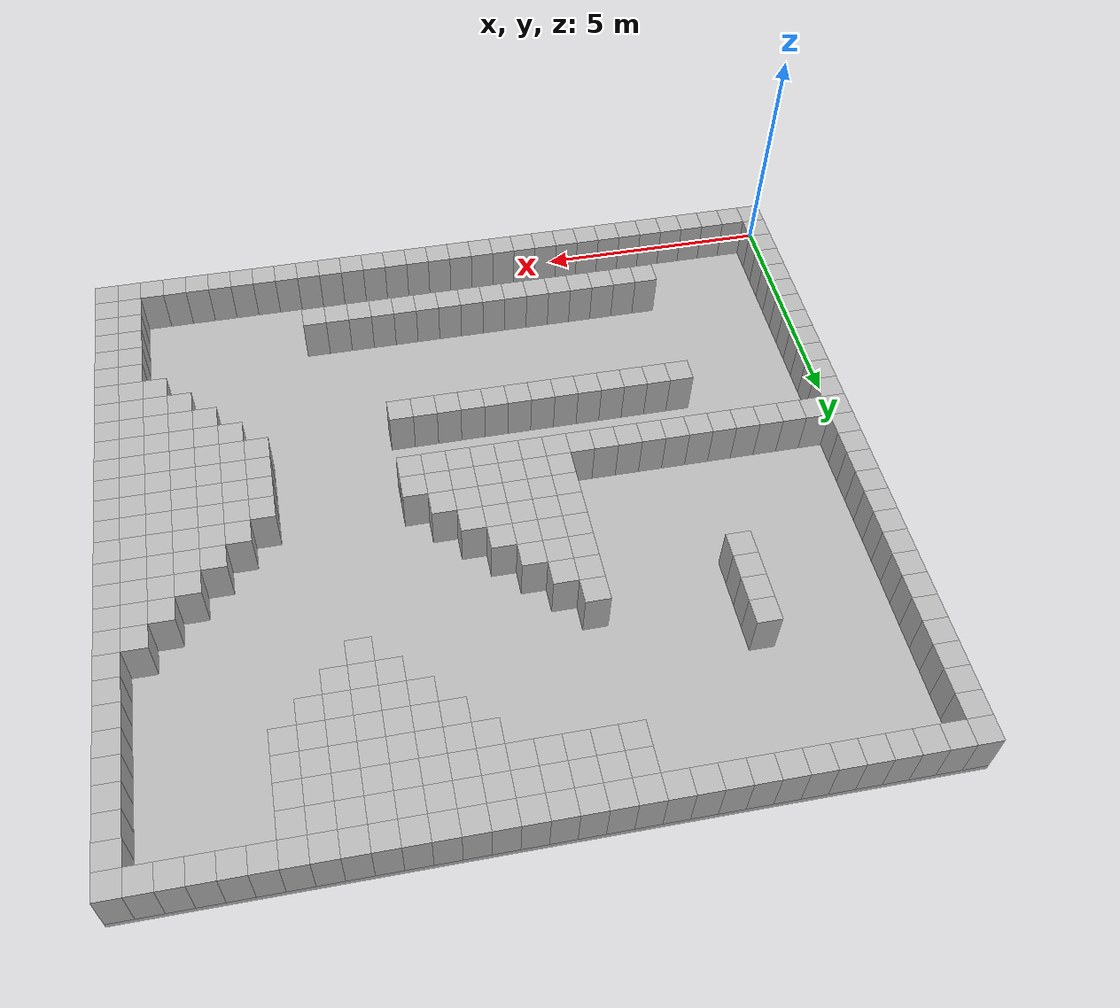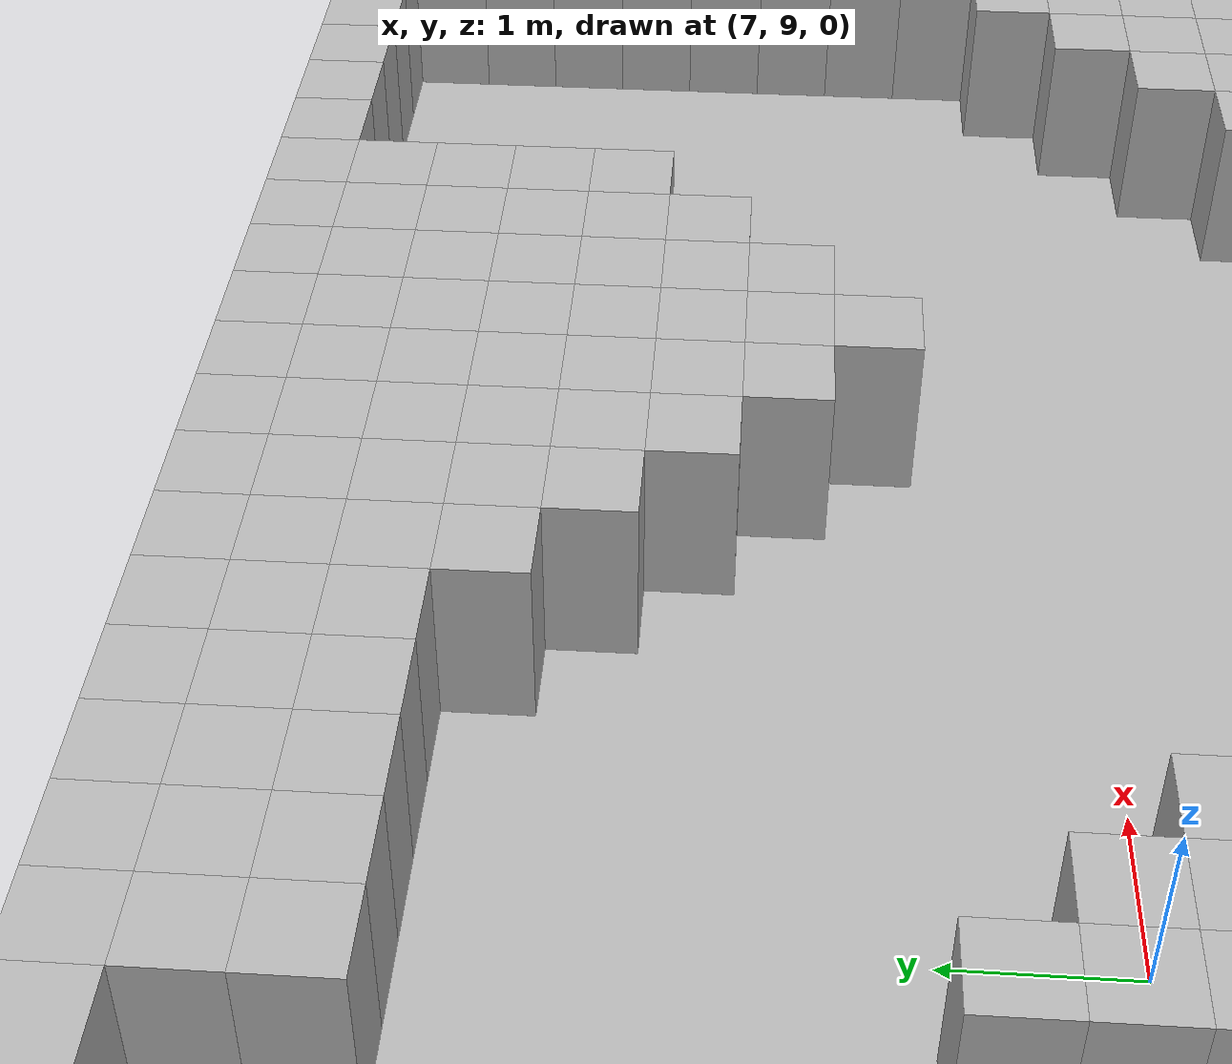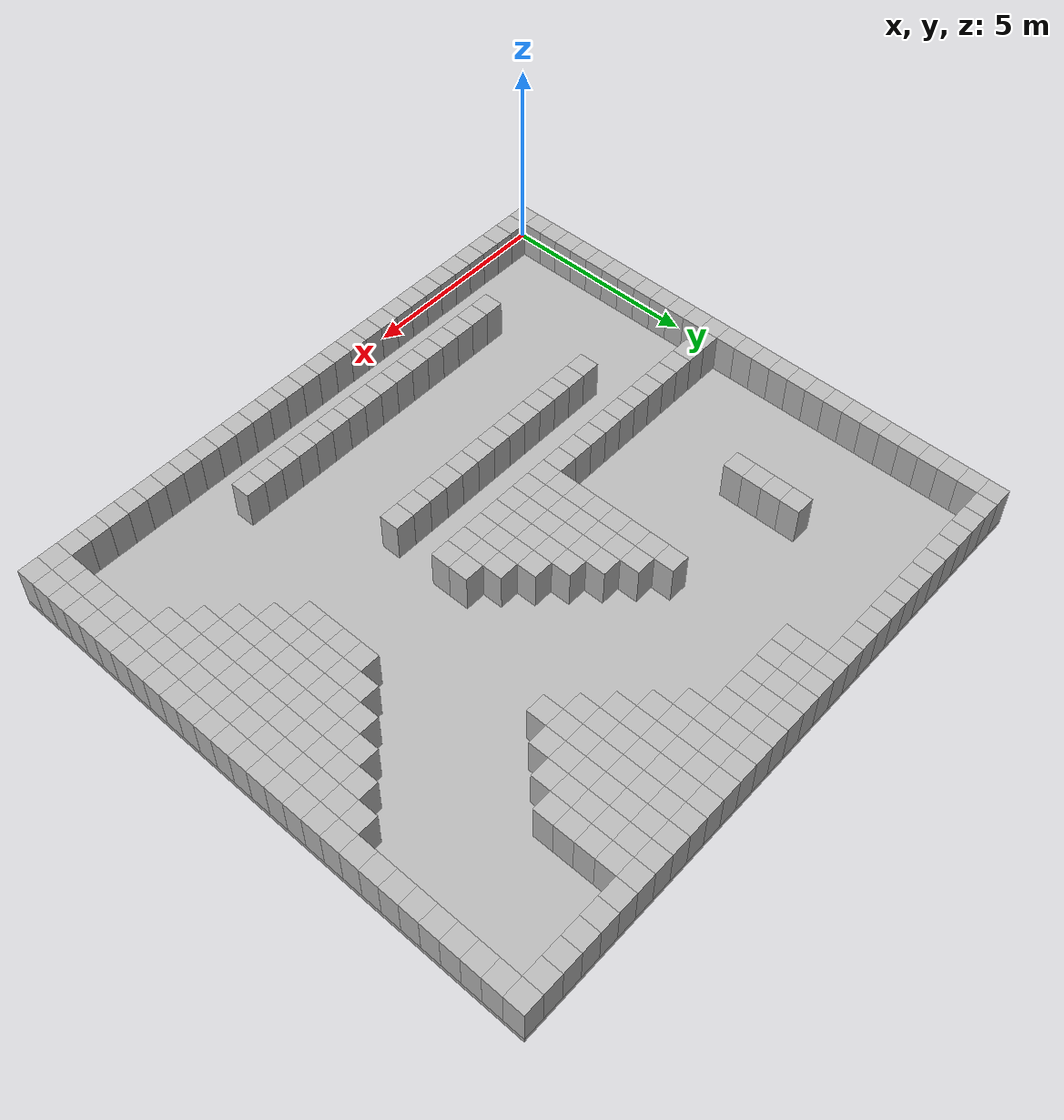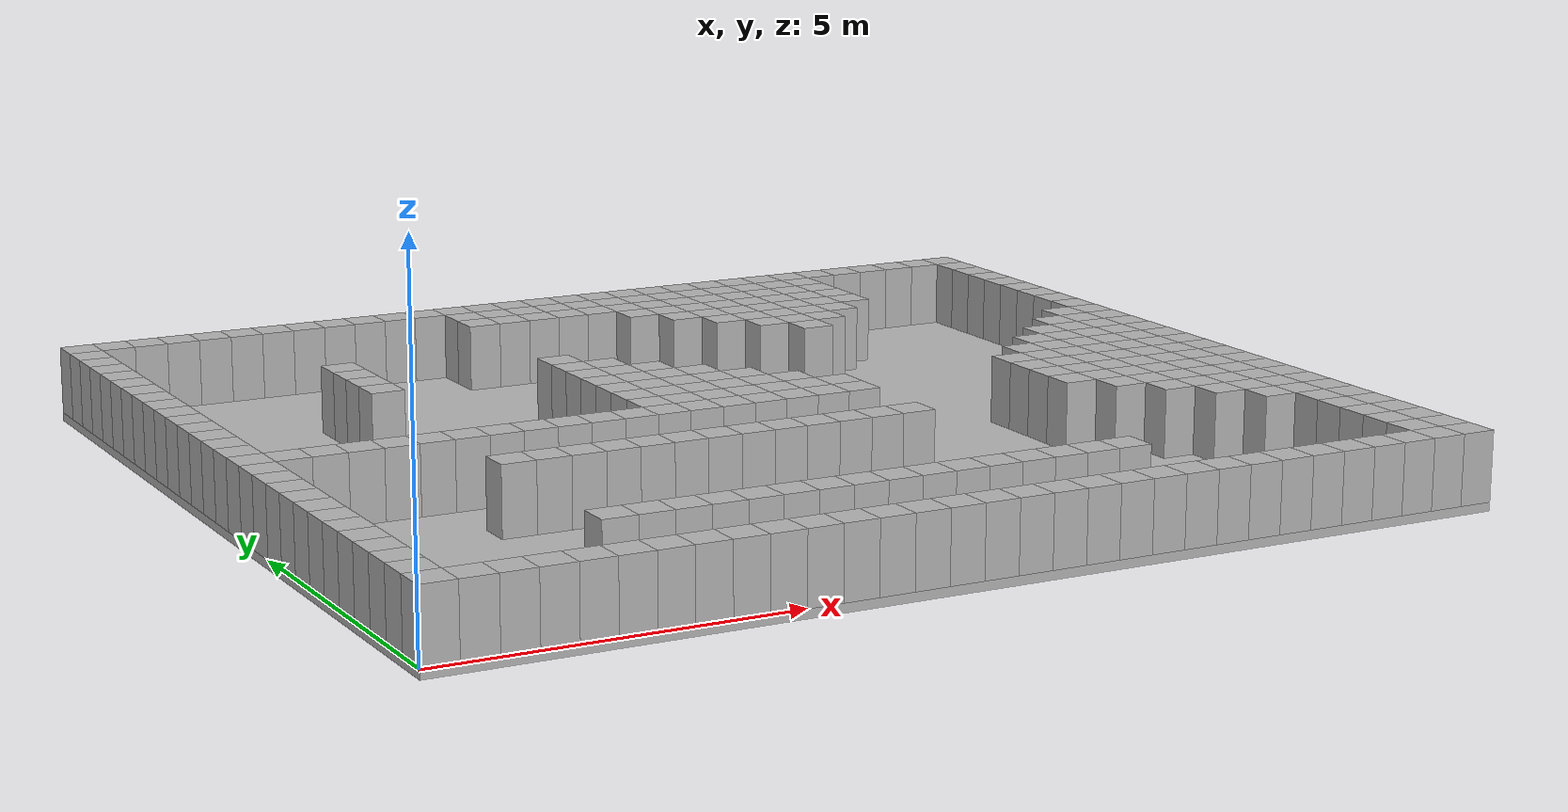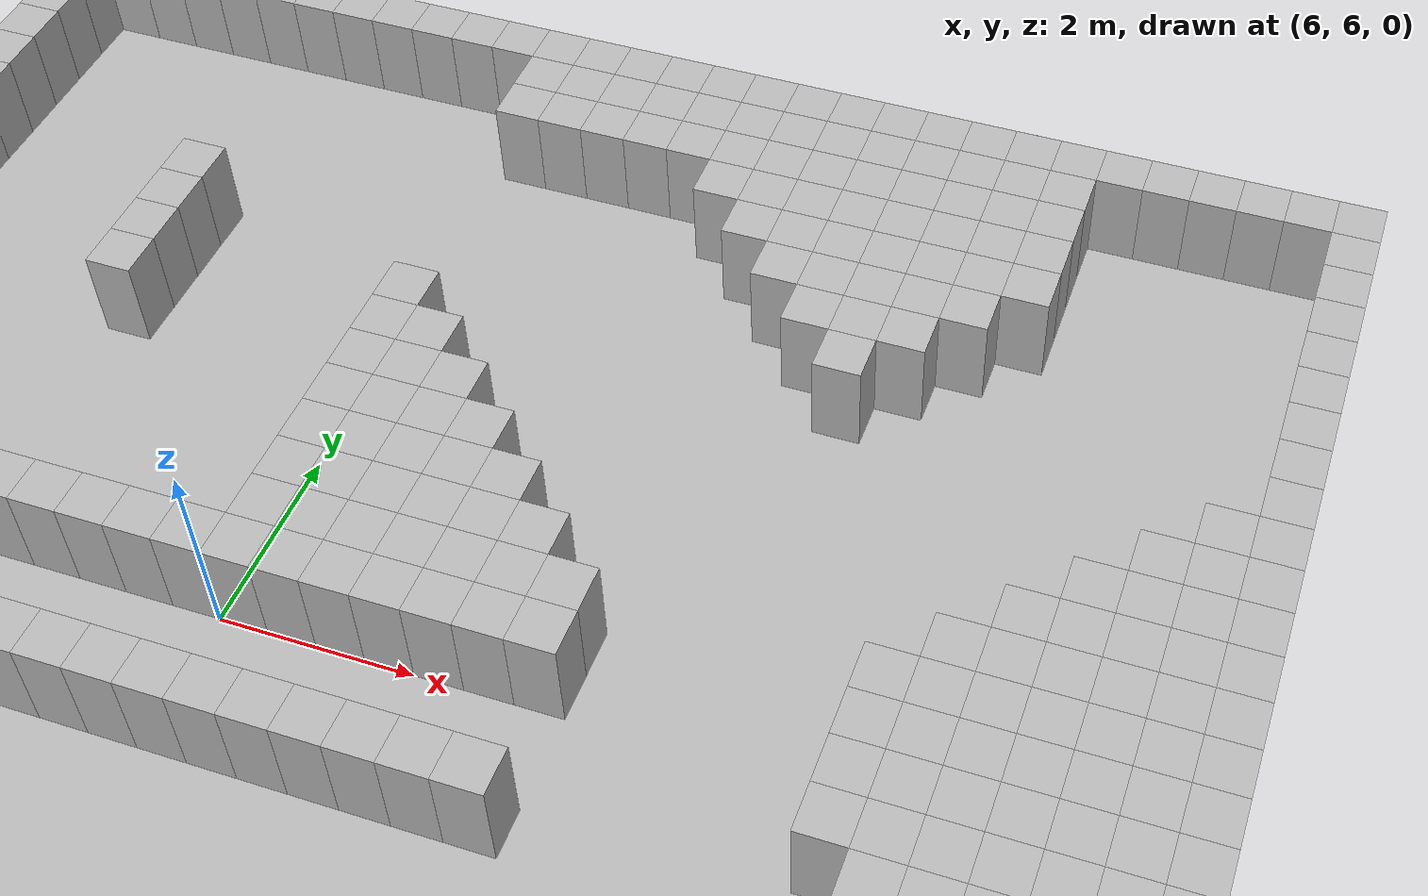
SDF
<sdf version="1.4">
  <world name="default">
    <light name="sun" type="directional">
      <cast_shadows>1</cast_shadows>
      <diffuse>0.8 0.8 0.8 1</diffuse>
      <specular>0.1 0.1 0.1 1</specular>
      <attenuation>
        <range>1000</range>
        <constant>0.9</constant>
        <linear>0.01</linear>
        <quadratic>0.001</quadratic>
      </attenuation>
      <direction>-0.5 0.5 -1</direction>
    </light>
    <model name="floor">
      <pose>7.75 7.0 -0.0625 0 0 0</pose>
      <static>true</static>
      <link name="link">
        <collision name="collision">
          <geometry>
            <box>
              <size>15.5 14.0 0.125</size>
            </box>
          </geometry>
        </collision>
        <visual name="visual">
          <geometry>
            <box>
              <size>15.5 14.0 0.125</size>
            </box>
          </geometry>
        </visual>
      </link>
    </model>
    <model name="box_0_0">
      <pose>0.25 0.25 0.5 0 0 0</pose>
      <static>true</static>
      <link name="link">
        <collision name="collision">
          <geometry>
            <box>
              <size>0.5 0.5 1.0</size>
            </box>
          </geometry>
        </collision>
        <visual name="visual">
          <geometry>
            <box>
              <size>0.5 0.5 1.0</size>
            </box>
          </geometry>
        </visual>
      </link>
    </model>
    <model name="box_0_1">
      <pose>0.25 0.75 0.5 0 0 0</pose>
      <static>true</static>
      <link name="link">
        <collision name="collision">
          <geometry>
            <box>
              <size>0.5 0.5 1.0</size>
            </box>
          </geometry>
        </collision>
        <visual name="visual">
          <geometry>
            <box>
              <size>0.5 0.5 1.0</size>
            </box>
          </geometry>
        </visual>
      </link>
    </model>
    <model name="box_0_2">
      <pose>0.25 1.25 0.5 0 0 0</pose>
      <static>true</static>
      <link name="link">
        <collision name="collision">
          <geometry>
            <box>
              <size>0.5 0.5 1.0</size>
            </box>
          </geometry>
        </collision>
        <visual name="visual">
          <geometry>
            <box>
              <size>0.5 0.5 1.0</size>
            </box>
          </geometry>
        </visual>
      </link>
    </model>
    <model name="box_0_3">
      <pose>0.25 1.75 0.5 0 0 0</pose>
      <static>true</static>
      <link name="link">
        <collision name="collision">
          <geometry>
            <box>
              <size>0.5 0.5 1.0</size>
            </box>
          </geometry>
        </collision>
        <visual name="visual">
          <geometry>
            <box>
              <size>0.5 0.5 1.0</size>
            </box>
          </geometry>
        </visual>
      </link>
    </model>
    <model name="box_0_4">
      <pose>0.25 2.25 0.5 0 0 0</pose>
      <static>true</static>
      <link name="link">
        <collision name="collision">
          <geometry>
            <box>
              <size>0.5 0.5 1.0</size>
            </box>
          </geometry>
        </collision>
        <visual name="visual">
          <geometry>
            <box>
              <size>0.5 0.5 1.0</size>
            </box>
          </geometry>
        </visual>
      </link>
    </model>
    <model name="box_0_5">
      <pose>0.25 2.75 0.5 0 0 0</pose>
      <static>true</static>
      <link name="link">
        <collision name="collision">
          <geometry>
            <box>
              <size>0.5 0.5 1.0</size>
            </box>
          </geometry>
        </collision>
        <visual name="visual">
          <geometry>
            <box>
              <size>0.5 0.5 1.0</size>
            </box>
          </geometry>
        </visual>
      </link>
    </model>
    <model name="box_0_6">
      <pose>0.25 3.25 0.5 0 0 0</pose>
      <static>true</static>
      <link name="link">
        <collision name="collision">
          <geometry>
            <box>
              <size>0.5 0.5 1.0</size>
            </box>
          </geometry>
        </collision>
        <visual name="visual">
          <geometry>
            <box>
              <size>0.5 0.5 1.0</size>
            </box>
          </geometry>
        </visual>
      </link>
    </model>
    <model name="box_0_7">
      <pose>0.25 3.75 0.5 0 0 0</pose>
      <static>true</static>
      <link name="link">
        <collision name="collision">
          <geometry>
            <box>
              <size>0.5 0.5 1.0</size>
            </box>
          </geometry>
        </collision>
        <visual name="visual">
          <geometry>
            <box>
              <size>0.5 0.5 1.0</size>
            </box>
          </geometry>
        </visual>
      </link>
    </model>
    <model name="box_0_8">
      <pose>0.25 4.25 0.5 0 0 0</pose>
      <static>true</static>
      <link name="link">
        <collision name="collision">
          <geometry>
            <box>
              <size>0.5 0.5 1.0</size>
            </box>
          </geometry>
        </collision>
        <visual name="visual">
          <geometry>
            <box>
              <size>0.5 0.5 1.0</size>
            </box>
          </geometry>
        </visual>
      </link>
    </model>
    <model name="box_0_9">
      <pose>0.25 4.75 0.5 0 0 0</pose>
      <static>true</static>
      <link name="link">
        <collision name="collision">
          <geometry>
            <box>
              <size>0.5 0.5 1.0</size>
            </box>
          </geometry>
        </collision>
        <visual name="visual">
          <geometry>
            <box>
              <size>0.5 0.5 1.0</size>
            </box>
          </geometry>
        </visual>
      </link>
    </model>
    <model name="box_0_10">
      <pose>0.25 5.25 0.5 0 0 0</pose>
      <static>true</static>
      <link name="link">
        <collision name="collision">
          <geometry>
            <box>
              <size>0.5 0.5 1.0</size>
            </box>
          </geometry>
        </collision>
        <visual name="visual">
          <geometry>
            <box>
              <size>0.5 0.5 1.0</size>
            </box>
          </geometry>
        </visual>
      </link>
    </model>
    <model name="box_0_11">
      <pose>0.25 5.75 0.5 0 0 0</pose>
      <static>true</static>
      <link name="link">
        <collision name="collision">
          <geometry>
            <box>
              <size>0.5 0.5 1.0</size>
            </box>
          </geometry>
        </collision>
        <visual name="visual">
          <geometry>
            <box>
              <size>0.5 0.5 1.0</size>
            </box>
          </geometry>
        </visual>
      </link>
    </model>
    <model name="box_0_12">
      <pose>0.25 6.25 0.5 0 0 0</pose>
      <static>true</static>
      <link name="link">
        <collision name="collision">
          <geometry>
            <box>
              <size>0.5 0.5 1.0</size>
            </box>
          </geometry>
        </collision>
        <visual name="visual">
          <geometry>
            <box>
              <size>0.5 0.5 1.0</size>
            </box>
          </geometry>
        </visual>
      </link>
    </model>
    <model name="box_0_13">
      <pose>0.25 6.75 0.5 0 0 0</pose>
      <static>true</static>
      <link name="link">
        <collision name="collision">
          <geometry>
            <box>
              <size>0.5 0.5 1.0</size>
            </box>
          </geometry>
        </collision>
        <visual name="visual">
          <geometry>
            <box>
              <size>0.5 0.5 1.0</size>
            </box>
          </geometry>
        </visual>
      </link>
    </model>
    <model name="box_0_14">
      <pose>0.25 7.25 0.5 0 0 0</pose>
      <static>true</static>
      <link name="link">
        <collision name="collision">
          <geometry>
            <box>
              <size>0.5 0.5 1.0</size>
            </box>
          </geometry>
        </collision>
        <visual name="visual">
          <geometry>
            <box>
              <size>0.5 0.5 1.0</size>
            </box>
          </geometry>
        </visual>
      </link>
    </model>
    <model name="box_0_15">
      <pose>0.25 7.75 0.5 0 0 0</pose>
      <static>true</static>
      <link name="link">
        <collision name="collision">
          <geometry>
            <box>
              <size>0.5 0.5 1.0</size>
            </box>
          </geometry>
        </collision>
        <visual name="visual">
          <geometry>
            <box>
              <size>0.5 0.5 1.0</size>
            </box>
          </geometry>
        </visual>
      </link>
    </model>
    <model name="box_0_16">
      <pose>0.25 8.25 0.5 0 0 0</pose>
      <static>true</static>
      <link name="link">
        <collision name="collision">
          <geometry>
            <box>
              <size>0.5 0.5 1.0</size>
            </box>
          </geometry>
        </collision>
        <visual name="visual">
          <geometry>
            <box>
              <size>0.5 0.5 1.0</size>
            </box>
          </geometry>
        </visual>
      </link>
    </model>
    <model name="box_0_17">
      <pose>0.25 8.75 0.5 0 0 0</pose>
      <static>true</static>
      <link name="link">
        <collision name="collision">
          <geometry>
            <box>
              <size>0.5 0.5 1.0</size>
            </box>
          </geometry>
        </collision>
        <visual name="visual">
          <geometry>
            <box>
              <size>0.5 0.5 1.0</size>
            </box>
          </geometry>
        </visual>
      </link>
    </model>
    <model name="box_0_18">
      <pose>0.25 9.25 0.5 0 0 0</pose>
      <static>true</static>
      <link name="link">
        <collision name="collision">
          <geometry>
            <box>
              <size>0.5 0.5 1.0</size>
            </box>
          </geometry>
        </collision>
        <visual name="visual">
          <geometry>
            <box>
              <size>0.5 0.5 1.0</size>
            </box>
          </geometry>
        </visual>
      </link>
    </model>
    <model name="box_0_19">
      <pose>0.25 9.75 0.5 0 0 0</pose>
      <static>true</static>
      <link name="link">
        <collision name="collision">
          <geometry>
            <box>
              <size>0.5 0.5 1.0</size>
            </box>
          </geometry>
        </collision>
        <visual name="visual">
          <geometry>
            <box>
              <size>0.5 0.5 1.0</size>
            </box>
          </geometry>
        </visual>
      </link>
    </model>
    <model name="box_0_20">
      <pose>0.25 10.25 0.5 0 0 0</pose>
      <static>true</static>
      <link name="link">
        <collision name="collision">
          <geometry>
            <box>
              <size>0.5 0.5 1.0</size>
            </box>
          </geometry>
        </collision>
        <visual name="visual">
          <geometry>
            <box>
              <size>0.5 0.5 1.0</size>
            </box>
          </geometry>
        </visual>
      </link>
    </model>
    <model name="box_0_21">
      <pose>0.25 10.75 0.5 0 0 0</pose>
      <static>true</static>
      <link name="link">
        <collision name="collision">
          <geometry>
            <box>
              <size>0.5 0.5 1.0</size>
            </box>
          </geometry>
        </collision>
        <visual name="visual">
          <geometry>
            <box>
              <size>0.5 0.5 1.0</size>
            </box>
          </geometry>
        </visual>
      </link>
    </model>
    <model name="box_0_22">
      <pose>0.25 11.25 0.5 0 0 0</pose>
      <static>true</static>
      <link name="link">
        <collision name="collision">
          <geometry>
            <box>
              <size>0.5 0.5 1.0</size>
            </box>
          </geometry>
        </collision>
        <visual name="visual">
          <geometry>
            <box>
              <size>0.5 0.5 1.0</size>
            </box>
          </geometry>
        </visual>
      </link>
    </model>
    <model name="box_0_23">
      <pose>0.25 11.75 0.5 0 0 0</pose>
      <static>true</static>
      <link name="link">
        <collision name="collision">
          <geometry>
            <box>
              <size>0.5 0.5 1.0</size>
            </box>
          </geometry>
        </collision>
        <visual name="visual">
          <geometry>
            <box>
              <size>0.5 0.5 1.0</size>
            </box>
          </geometry>
        </visual>
      </link>
    </model>
    <model name="box_0_24">
      <pose>0.25 12.25 0.5 0 0 0</pose>
      <static>true</static>
      <link name="link">
        <collision name="collision">
          <geometry>
            <box>
              <size>0.5 0.5 1.0</size>
            </box>
          </geometry>
        </collision>
        <visual name="visual">
          <geometry>
            <box>
              <size>0.5 0.5 1.0</size>
            </box>
          </geometry>
        </visual>
      </link>
    </model>
    <model name="box_0_25">
      <pose>0.25 12.75 0.5 0 0 0</pose>
      <static>true</static>
      <link name="link">
        <collision name="collision">
          <geometry>
            <box>
              <size>0.5 0.5 1.0</size>
            </box>
          </geometry>
        </collision>
        <visual name="visual">
          <geometry>
            <box>
              <size>0.5 0.5 1.0</size>
            </box>
          </geometry>
        </visual>
      </link>
    </model>
    <model name="box_0_26">
      <pose>0.25 13.25 0.5 0 0 0</pose>
      <static>true</static>
      <link name="link">
        <collision name="collision">
          <geometry>
            <box>
              <size>0.5 0.5 1.0</size>
            </box>
          </geometry>
        </collision>
        <visual name="visual">
          <geometry>
            <box>
              <size>0.5 0.5 1.0</size>
            </box>
          </geometry>
        </visual>
      </link>
    </model>
    <model name="box_0_27">
      <pose>0.25 13.75 0.5 0 0 0</pose>
      <static>true</static>
      <link name="link">
        <collision name="collision">
          <geometry>
            <box>
              <size>0.5 0.5 1.0</size>
            </box>
          </geometry>
        </collision>
        <visual name="visual">
          <geometry>
            <box>
              <size>0.5 0.5 1.0</size>
            </box>
          </geometry>
        </visual>
      </link>
    </model>
    <model name="box_1_0">
      <pose>0.75 0.25 0.5 0 0 0</pose>
      <static>true</static>
      <link name="link">
        <collision name="collision">
          <geometry>
            <box>
              <size>0.5 0.5 1.0</size>
            </box>
          </geometry>
        </collision>
        <visual name="visual">
          <geometry>
            <box>
              <size>0.5 0.5 1.0</size>
            </box>
          </geometry>
        </visual>
      </link>
    </model>
    <model name="box_1_12">
      <pose>0.75 6.25 0.5 0 0 0</pose>
      <static>true</static>
      <link name="link">
        <collision name="collision">
          <geometry>
            <box>
              <size>0.5 0.5 1.0</size>
            </box>
          </geometry>
        </collision>
        <visual name="visual">
          <geometry>
            <box>
              <size>0.5 0.5 1.0</size>
            </box>
          </geometry>
        </visual>
      </link>
    </model>
    <model name="box_1_27">
      <pose>0.75 13.75 0.5 0 0 0</pose>
      <static>true</static>
      <link name="link">
        <collision name="collision">
          <geometry>
            <box>
              <size>0.5 0.5 1.0</size>
            </box>
          </geometry>
        </collision>
        <visual name="visual">
          <geometry>
            <box>
              <size>0.5 0.5 1.0</size>
            </box>
          </geometry>
        </visual>
      </link>
    </model>
    <model name="box_2_0">
      <pose>1.25 0.25 0.5 0 0 0</pose>
      <static>true</static>
      <link name="link">
        <collision name="collision">
          <geometry>
            <box>
              <size>0.5 0.5 1.0</size>
            </box>
          </geometry>
        </collision>
        <visual name="visual">
          <geometry>
            <box>
              <size>0.5 0.5 1.0</size>
            </box>
          </geometry>
        </visual>
      </link>
    </model>
    <model name="box_2_12">
      <pose>1.25 6.25 0.5 0 0 0</pose>
      <static>true</static>
      <link name="link">
        <collision name="collision">
          <geometry>
            <box>
              <size>0.5 0.5 1.0</size>
            </box>
          </geometry>
        </collision>
        <visual name="visual">
          <geometry>
            <box>
              <size>0.5 0.5 1.0</size>
            </box>
          </geometry>
        </visual>
      </link>
    </model>
    <model name="box_2_27">
      <pose>1.25 13.75 0.5 0 0 0</pose>
      <static>true</static>
      <link name="link">
        <collision name="collision">
          <geometry>
            <box>
              <size>0.5 0.5 1.0</size>
            </box>
          </geometry>
        </collision>
        <visual name="visual">
          <geometry>
            <box>
              <size>0.5 0.5 1.0</size>
            </box>
          </geometry>
        </visual>
      </link>
    </model>
    <model name="box_3_0">
      <pose>1.75 0.25 0.5 0 0 0</pose>
      <static>true</static>
      <link name="link">
        <collision name="collision">
          <geometry>
            <box>
              <size>0.5 0.5 1.0</size>
            </box>
          </geometry>
        </collision>
        <visual name="visual">
          <geometry>
            <box>
              <size>0.5 0.5 1.0</size>
            </box>
          </geometry>
        </visual>
      </link>
    </model>
    <model name="box_3_12">
      <pose>1.75 6.25 0.5 0 0 0</pose>
      <static>true</static>
      <link name="link">
        <collision name="collision">
          <geometry>
            <box>
              <size>0.5 0.5 1.0</size>
            </box>
          </geometry>
        </collision>
        <visual name="visual">
          <geometry>
            <box>
              <size>0.5 0.5 1.0</size>
            </box>
          </geometry>
        </visual>
      </link>
    </model>
    <model name="box_3_27">
      <pose>1.75 13.75 0.5 0 0 0</pose>
      <static>true</static>
      <link name="link">
        <collision name="collision">
          <geometry>
            <box>
              <size>0.5 0.5 1.0</size>
            </box>
          </geometry>
        </collision>
        <visual name="visual">
          <geometry>
            <box>
              <size>0.5 0.5 1.0</size>
            </box>
          </geometry>
        </visual>
      </link>
    </model>
    <model name="box_4_0">
      <pose>2.25 0.25 0.5 0 0 0</pose>
      <static>true</static>
      <link name="link">
        <collision name="collision">
          <geometry>
            <box>
              <size>0.5 0.5 1.0</size>
            </box>
          </geometry>
        </collision>
        <visual name="visual">
          <geometry>
            <box>
              <size>0.5 0.5 1.0</size>
            </box>
          </geometry>
        </visual>
      </link>
    </model>
    <model name="box_4_12">
      <pose>2.25 6.25 0.5 0 0 0</pose>
      <static>true</static>
      <link name="link">
        <collision name="collision">
          <geometry>
            <box>
              <size>0.5 0.5 1.0</size>
            </box>
          </geometry>
        </collision>
        <visual name="visual">
          <geometry>
            <box>
              <size>0.5 0.5 1.0</size>
            </box>
          </geometry>
        </visual>
      </link>
    </model>
    <model name="box_4_27">
      <pose>2.25 13.75 0.5 0 0 0</pose>
      <static>true</static>
      <link name="link">
        <collision name="collision">
          <geometry>
            <box>
              <size>0.5 0.5 1.0</size>
            </box>
          </geometry>
        </collision>
        <visual name="visual">
          <geometry>
            <box>
              <size>0.5 0.5 1.0</size>
            </box>
          </geometry>
        </visual>
      </link>
    </model>
    <model name="box_5_0">
      <pose>2.75 0.25 0.5 0 0 0</pose>
      <static>true</static>
      <link name="link">
        <collision name="collision">
          <geometry>
            <box>
              <size>0.5 0.5 1.0</size>
            </box>
          </geometry>
        </collision>
        <visual name="visual">
          <geometry>
            <box>
              <size>0.5 0.5 1.0</size>
            </box>
          </geometry>
        </visual>
      </link>
    </model>
    <model name="box_5_12">
      <pose>2.75 6.25 0.5 0 0 0</pose>
      <static>true</static>
      <link name="link">
        <collision name="collision">
          <geometry>
            <box>
              <size>0.5 0.5 1.0</size>
            </box>
          </geometry>
        </collision>
        <visual name="visual">
          <geometry>
            <box>
              <size>0.5 0.5 1.0</size>
            </box>
          </geometry>
        </visual>
      </link>
    </model>
    <model name="box_5_27">
      <pose>2.75 13.75 0.5 0 0 0</pose>
      <static>true</static>
      <link name="link">
        <collision name="collision">
          <geometry>
            <box>
              <size>0.5 0.5 1.0</size>
            </box>
          </geometry>
        </collision>
        <visual name="visual">
          <geometry>
            <box>
              <size>0.5 0.5 1.0</size>
            </box>
          </geometry>
        </visual>
      </link>
    </model>
    <model name="box_6_0">
      <pose>3.25 0.25 0.5 0 0 0</pose>
      <static>true</static>
      <link name="link">
        <collision name="collision">
          <geometry>
            <box>
              <size>0.5 0.5 1.0</size>
            </box>
          </geometry>
        </collision>
        <visual name="visual">
          <geometry>
            <box>
              <size>0.5 0.5 1.0</size>
            </box>
          </geometry>
        </visual>
      </link>
    </model>
    <model name="box_6_3">
      <pose>3.25 1.75 0.5 0 0 0</pose>
      <static>true</static>
      <link name="link">
        <collision name="collision">
          <geometry>
            <box>
              <size>0.5 0.5 1.0</size>
            </box>
          </geometry>
        </collision>
        <visual name="visual">
          <geometry>
            <box>
              <size>0.5 0.5 1.0</size>
            </box>
          </geometry>
        </visual>
      </link>
    </model>
    <model name="box_6_9">
      <pose>3.25 4.75 0.5 0 0 0</pose>
      <static>true</static>
      <link name="link">
        <collision name="collision">
          <geometry>
            <box>
              <size>0.5 0.5 1.0</size>
            </box>
          </geometry>
        </collision>
        <visual name="visual">
          <geometry>
            <box>
              <size>0.5 0.5 1.0</size>
            </box>
          </geometry>
        </visual>
      </link>
    </model>
    <model name="box_6_12">
      <pose>3.25 6.25 0.5 0 0 0</pose>
      <static>true</static>
      <link name="link">
        <collision name="collision">
          <geometry>
            <box>
              <size>0.5 0.5 1.0</size>
            </box>
          </geometry>
        </collision>
        <visual name="visual">
          <geometry>
            <box>
              <size>0.5 0.5 1.0</size>
            </box>
          </geometry>
        </visual>
      </link>
    </model>
    <model name="box_6_18">
      <pose>3.25 9.25 0.5 0 0 0</pose>
      <static>true</static>
      <link name="link">
        <collision name="collision">
          <geometry>
            <box>
              <size>0.5 0.5 1.0</size>
            </box>
          </geometry>
        </collision>
        <visual name="visual">
          <geometry>
            <box>
              <size>0.5 0.5 1.0</size>
            </box>
          </geometry>
        </visual>
      </link>
    </model>
    <model name="box_6_19">
      <pose>3.25 9.75 0.5 0 0 0</pose>
      <static>true</static>
      <link name="link">
        <collision name="collision">
          <geometry>
            <box>
              <size>0.5 0.5 1.0</size>
            </box>
          </geometry>
        </collision>
        <visual name="visual">
          <geometry>
            <box>
              <size>0.5 0.5 1.0</size>
            </box>
          </geometry>
        </visual>
      </link>
    </model>
    <model name="box_6_20">
      <pose>3.25 10.25 0.5 0 0 0</pose>
      <static>true</static>
      <link name="link">
        <collision name="collision">
          <geometry>
            <box>
              <size>0.5 0.5 1.0</size>
            </box>
          </geometry>
        </collision>
        <visual name="visual">
          <geometry>
            <box>
              <size>0.5 0.5 1.0</size>
            </box>
          </geometry>
        </visual>
      </link>
    </model>
    <model name="box_6_21">
      <pose>3.25 10.75 0.5 0 0 0</pose>
      <static>true</static>
      <link name="link">
        <collision name="collision">
          <geometry>
            <box>
              <size>0.5 0.5 1.0</size>
            </box>
          </geometry>
        </collision>
        <visual name="visual">
          <geometry>
            <box>
              <size>0.5 0.5 1.0</size>
            </box>
          </geometry>
        </visual>
      </link>
    </model>
    <model name="box_6_27">
      <pose>3.25 13.75 0.5 0 0 0</pose>
      <static>true</static>
      <link name="link">
        <collision name="collision">
          <geometry>
            <box>
              <size>0.5 0.5 1.0</size>
            </box>
          </geometry>
        </collision>
        <visual name="visual">
          <geometry>
            <box>
              <size>0.5 0.5 1.0</size>
            </box>
          </geometry>
        </visual>
      </link>
    </model>
    <model name="box_7_0">
      <pose>3.75 0.25 0.5 0 0 0</pose>
      <static>true</static>
      <link name="link">
        <collision name="collision">
          <geometry>
            <box>
              <size>0.5 0.5 1.0</size>
            </box>
          </geometry>
        </collision>
        <visual name="visual">
          <geometry>
            <box>
              <size>0.5 0.5 1.0</size>
            </box>
          </geometry>
        </visual>
      </link>
    </model>
    <model name="box_7_3">
      <pose>3.75 1.75 0.5 0 0 0</pose>
      <static>true</static>
      <link name="link">
        <collision name="collision">
          <geometry>
            <box>
              <size>0.5 0.5 1.0</size>
            </box>
          </geometry>
        </collision>
        <visual name="visual">
          <geometry>
            <box>
              <size>0.5 0.5 1.0</size>
            </box>
          </geometry>
        </visual>
      </link>
    </model>
    <model name="box_7_9">
      <pose>3.75 4.75 0.5 0 0 0</pose>
      <static>true</static>
      <link name="link">
        <collision name="collision">
          <geometry>
            <box>
              <size>0.5 0.5 1.0</size>
            </box>
          </geometry>
        </collision>
        <visual name="visual">
          <geometry>
            <box>
              <size>0.5 0.5 1.0</size>
            </box>
          </geometry>
        </visual>
      </link>
    </model>
    <model name="box_7_12">
      <pose>3.75 6.25 0.5 0 0 0</pose>
      <static>true</static>
      <link name="link">
        <collision name="collision">
          <geometry>
            <box>
              <size>0.5 0.5 1.0</size>
            </box>
          </geometry>
        </collision>
        <visual name="visual">
          <geometry>
            <box>
              <size>0.5 0.5 1.0</size>
            </box>
          </geometry>
        </visual>
      </link>
    </model>
    <model name="box_7_27">
      <pose>3.75 13.75 0.5 0 0 0</pose>
      <static>true</static>
      <link name="link">
        <collision name="collision">
          <geometry>
            <box>
              <size>0.5 0.5 1.0</size>
            </box>
          </geometry>
        </collision>
        <visual name="visual">
          <geometry>
            <box>
              <size>0.5 0.5 1.0</size>
            </box>
          </geometry>
        </visual>
      </link>
    </model>
    <model name="box_8_0">
      <pose>4.25 0.25 0.5 0 0 0</pose>
      <static>true</static>
      <link name="link">
        <collision name="collision">
          <geometry>
            <box>
              <size>0.5 0.5 1.0</size>
            </box>
          </geometry>
        </collision>
        <visual name="visual">
          <geometry>
            <box>
              <size>0.5 0.5 1.0</size>
            </box>
          </geometry>
        </visual>
      </link>
    </model>
    <model name="box_8_3">
      <pose>4.25 1.75 0.5 0 0 0</pose>
      <static>true</static>
      <link name="link">
        <collision name="collision">
          <geometry>
            <box>
              <size>0.5 0.5 1.0</size>
            </box>
          </geometry>
        </collision>
        <visual name="visual">
          <geometry>
            <box>
              <size>0.5 0.5 1.0</size>
            </box>
          </geometry>
        </visual>
      </link>
    </model>
    <model name="box_8_9">
      <pose>4.25 4.75 0.5 0 0 0</pose>
      <static>true</static>
      <link name="link">
        <collision name="collision">
          <geometry>
            <box>
              <size>0.5 0.5 1.0</size>
            </box>
          </geometry>
        </collision>
        <visual name="visual">
          <geometry>
            <box>
              <size>0.5 0.5 1.0</size>
            </box>
          </geometry>
        </visual>
      </link>
    </model>
    <model name="box_8_12">
      <pose>4.25 6.25 0.5 0 0 0</pose>
      <static>true</static>
      <link name="link">
        <collision name="collision">
          <geometry>
            <box>
              <size>0.5 0.5 1.0</size>
            </box>
          </geometry>
        </collision>
        <visual name="visual">
          <geometry>
            <box>
              <size>0.5 0.5 1.0</size>
            </box>
          </geometry>
        </visual>
      </link>
    </model>
    <model name="box_8_27">
      <pose>4.25 13.75 0.5 0 0 0</pose>
      <static>true</static>
      <link name="link">
        <collision name="collision">
          <geometry>
            <box>
              <size>0.5 0.5 1.0</size>
            </box>
          </geometry>
        </collision>
        <visual name="visual">
          <geometry>
            <box>
              <size>0.5 0.5 1.0</size>
            </box>
          </geometry>
        </visual>
      </link>
    </model>
    <model name="box_9_0">
      <pose>4.75 0.25 0.5 0 0 0</pose>
      <static>true</static>
      <link name="link">
        <collision name="collision">
          <geometry>
            <box>
              <size>0.5 0.5 1.0</size>
            </box>
          </geometry>
        </collision>
        <visual name="visual">
          <geometry>
            <box>
              <size>0.5 0.5 1.0</size>
            </box>
          </geometry>
        </visual>
      </link>
    </model>
    <model name="box_9_3">
      <pose>4.75 1.75 0.5 0 0 0</pose>
      <static>true</static>
      <link name="link">
        <collision name="collision">
          <geometry>
            <box>
              <size>0.5 0.5 1.0</size>
            </box>
          </geometry>
        </collision>
        <visual name="visual">
          <geometry>
            <box>
              <size>0.5 0.5 1.0</size>
            </box>
          </geometry>
        </visual>
      </link>
    </model>
    <model name="box_9_9">
      <pose>4.75 4.75 0.5 0 0 0</pose>
      <static>true</static>
      <link name="link">
        <collision name="collision">
          <geometry>
            <box>
              <size>0.5 0.5 1.0</size>
            </box>
          </geometry>
        </collision>
        <visual name="visual">
          <geometry>
            <box>
              <size>0.5 0.5 1.0</size>
            </box>
          </geometry>
        </visual>
      </link>
    </model>
    <model name="box_9_12">
      <pose>4.75 6.25 0.5 0 0 0</pose>
      <static>true</static>
      <link name="link">
        <collision name="collision">
          <geometry>
            <box>
              <size>0.5 0.5 1.0</size>
            </box>
          </geometry>
        </collision>
        <visual name="visual">
          <geometry>
            <box>
              <size>0.5 0.5 1.0</size>
            </box>
          </geometry>
        </visual>
      </link>
    </model>
    <model name="box_9_27">
      <pose>4.75 13.75 0.5 0 0 0</pose>
      <static>true</static>
      <link name="link">
        <collision name="collision">
          <geometry>
            <box>
              <size>0.5 0.5 1.0</size>
            </box>
          </geometry>
        </collision>
        <visual name="visual">
          <geometry>
            <box>
              <size>0.5 0.5 1.0</size>
            </box>
          </geometry>
        </visual>
      </link>
    </model>
    <model name="box_10_0">
      <pose>5.25 0.25 0.5 0 0 0</pose>
      <static>true</static>
      <link name="link">
        <collision name="collision">
          <geometry>
            <box>
              <size>0.5 0.5 1.0</size>
            </box>
          </geometry>
        </collision>
        <visual name="visual">
          <geometry>
            <box>
              <size>0.5 0.5 1.0</size>
            </box>
          </geometry>
        </visual>
      </link>
    </model>
    <model name="box_10_3">
      <pose>5.25 1.75 0.5 0 0 0</pose>
      <static>true</static>
      <link name="link">
        <collision name="collision">
          <geometry>
            <box>
              <size>0.5 0.5 1.0</size>
            </box>
          </geometry>
        </collision>
        <visual name="visual">
          <geometry>
            <box>
              <size>0.5 0.5 1.0</size>
            </box>
          </geometry>
        </visual>
      </link>
    </model>
    <model name="box_10_9">
      <pose>5.25 4.75 0.5 0 0 0</pose>
      <static>true</static>
      <link name="link">
        <collision name="collision">
          <geometry>
            <box>
              <size>0.5 0.5 1.0</size>
            </box>
          </geometry>
        </collision>
        <visual name="visual">
          <geometry>
            <box>
              <size>0.5 0.5 1.0</size>
            </box>
          </geometry>
        </visual>
      </link>
    </model>
    <model name="box_10_12">
      <pose>5.25 6.25 0.5 0 0 0</pose>
      <static>true</static>
      <link name="link">
        <collision name="collision">
          <geometry>
            <box>
              <size>0.5 0.5 1.0</size>
            </box>
          </geometry>
        </collision>
        <visual name="visual">
          <geometry>
            <box>
              <size>0.5 0.5 1.0</size>
            </box>
          </geometry>
        </visual>
      </link>
    </model>
    <model name="box_10_27">
      <pose>5.25 13.75 0.5 0 0 0</pose>
      <static>true</static>
      <link name="link">
        <collision name="collision">
          <geometry>
            <box>
              <size>0.5 0.5 1.0</size>
            </box>
          </geometry>
        </collision>
        <visual name="visual">
          <geometry>
            <box>
              <size>0.5 0.5 1.0</size>
            </box>
          </geometry>
        </visual>
      </link>
    </model>
    <model name="box_11_0">
      <pose>5.75 0.25 0.5 0 0 0</pose>
      <static>true</static>
      <link name="link">
        <collision name="collision">
          <geometry>
            <box>
              <size>0.5 0.5 1.0</size>
            </box>
          </geometry>
        </collision>
        <visual name="visual">
          <geometry>
            <box>
              <size>0.5 0.5 1.0</size>
            </box>
          </geometry>
        </visual>
      </link>
    </model>
    <model name="box_11_3">
      <pose>5.75 1.75 0.5 0 0 0</pose>
      <static>true</static>
      <link name="link">
        <collision name="collision">
          <geometry>
            <box>
              <size>0.5 0.5 1.0</size>
            </box>
          </geometry>
        </collision>
        <visual name="visual">
          <geometry>
            <box>
              <size>0.5 0.5 1.0</size>
            </box>
          </geometry>
        </visual>
      </link>
    </model>
    <model name="box_11_9">
      <pose>5.75 4.75 0.5 0 0 0</pose>
      <static>true</static>
      <link name="link">
        <collision name="collision">
          <geometry>
            <box>
              <size>0.5 0.5 1.0</size>
            </box>
          </geometry>
        </collision>
        <visual name="visual">
          <geometry>
            <box>
              <size>0.5 0.5 1.0</size>
            </box>
          </geometry>
        </visual>
      </link>
    </model>
    <model name="box_11_12">
      <pose>5.75 6.25 0.5 0 0 0</pose>
      <static>true</static>
      <link name="link">
        <collision name="collision">
          <geometry>
            <box>
              <size>0.5 0.5 1.0</size>
            </box>
          </geometry>
        </collision>
        <visual name="visual">
          <geometry>
            <box>
              <size>0.5 0.5 1.0</size>
            </box>
          </geometry>
        </visual>
      </link>
    </model>
    <model name="box_11_27">
      <pose>5.75 13.75 0.5 0 0 0</pose>
      <static>true</static>
      <link name="link">
        <collision name="collision">
          <geometry>
            <box>
              <size>0.5 0.5 1.0</size>
            </box>
          </geometry>
        </collision>
        <visual name="visual">
          <geometry>
            <box>
              <size>0.5 0.5 1.0</size>
            </box>
          </geometry>
        </visual>
      </link>
    </model>
    <model name="box_12_0">
      <pose>6.25 0.25 0.5 0 0 0</pose>
      <static>true</static>
      <link name="link">
        <collision name="collision">
          <geometry>
            <box>
              <size>0.5 0.5 1.0</size>
            </box>
          </geometry>
        </collision>
        <visual name="visual">
          <geometry>
            <box>
              <size>0.5 0.5 1.0</size>
            </box>
          </geometry>
        </visual>
      </link>
    </model>
    <model name="box_12_3">
      <pose>6.25 1.75 0.5 0 0 0</pose>
      <static>true</static>
      <link name="link">
        <collision name="collision">
          <geometry>
            <box>
              <size>0.5 0.5 1.0</size>
            </box>
          </geometry>
        </collision>
        <visual name="visual">
          <geometry>
            <box>
              <size>0.5 0.5 1.0</size>
            </box>
          </geometry>
        </visual>
      </link>
    </model>
    <model name="box_12_9">
      <pose>6.25 4.75 0.5 0 0 0</pose>
      <static>true</static>
      <link name="link">
        <collision name="collision">
          <geometry>
            <box>
              <size>0.5 0.5 1.0</size>
            </box>
          </geometry>
        </collision>
        <visual name="visual">
          <geometry>
            <box>
              <size>0.5 0.5 1.0</size>
            </box>
          </geometry>
        </visual>
      </link>
    </model>
    <model name="box_12_12">
      <pose>6.25 6.25 0.5 0 0 0</pose>
      <static>true</static>
      <link name="link">
        <collision name="collision">
          <geometry>
            <box>
              <size>0.5 0.5 1.0</size>
            </box>
          </geometry>
        </collision>
        <visual name="visual">
          <geometry>
            <box>
              <size>0.5 0.5 1.0</size>
            </box>
          </geometry>
        </visual>
      </link>
    </model>
    <model name="box_12_13">
      <pose>6.25 6.75 0.5 0 0 0</pose>
      <static>true</static>
      <link name="link">
        <collision name="collision">
          <geometry>
            <box>
              <size>0.5 0.5 1.0</size>
            </box>
          </geometry>
        </collision>
        <visual name="visual">
          <geometry>
            <box>
              <size>0.5 0.5 1.0</size>
            </box>
          </geometry>
        </visual>
      </link>
    </model>
    <model name="box_12_14">
      <pose>6.25 7.25 0.5 0 0 0</pose>
      <static>true</static>
      <link name="link">
        <collision name="collision">
          <geometry>
            <box>
              <size>0.5 0.5 1.0</size>
            </box>
          </geometry>
        </collision>
        <visual name="visual">
          <geometry>
            <box>
              <size>0.5 0.5 1.0</size>
            </box>
          </geometry>
        </visual>
      </link>
    </model>
    <model name="box_12_15">
      <pose>6.25 7.75 0.5 0 0 0</pose>
      <static>true</static>
      <link name="link">
        <collision name="collision">
          <geometry>
            <box>
              <size>0.5 0.5 1.0</size>
            </box>
          </geometry>
        </collision>
        <visual name="visual">
          <geometry>
            <box>
              <size>0.5 0.5 1.0</size>
            </box>
          </geometry>
        </visual>
      </link>
    </model>
    <model name="box_12_16">
      <pose>6.25 8.25 0.5 0 0 0</pose>
      <static>true</static>
      <link name="link">
        <collision name="collision">
          <geometry>
            <box>
              <size>0.5 0.5 1.0</size>
            </box>
          </geometry>
        </collision>
        <visual name="visual">
          <geometry>
            <box>
              <size>0.5 0.5 1.0</size>
            </box>
          </geometry>
        </visual>
      </link>
    </model>
    <model name="box_12_17">
      <pose>6.25 8.75 0.5 0 0 0</pose>
      <static>true</static>
      <link name="link">
        <collision name="collision">
          <geometry>
            <box>
              <size>0.5 0.5 1.0</size>
            </box>
          </geometry>
        </collision>
        <visual name="visual">
          <geometry>
            <box>
              <size>0.5 0.5 1.0</size>
            </box>
          </geometry>
        </visual>
      </link>
    </model>
    <model name="box_12_18">
      <pose>6.25 9.25 0.5 0 0 0</pose>
      <static>true</static>
      <link name="link">
        <collision name="collision">
          <geometry>
            <box>
              <size>0.5 0.5 1.0</size>
            </box>
          </geometry>
        </collision>
        <visual name="visual">
          <geometry>
            <box>
              <size>0.5 0.5 1.0</size>
            </box>
          </geometry>
        </visual>
      </link>
    </model>
    <model name="box_12_19">
      <pose>6.25 9.75 0.5 0 0 0</pose>
      <static>true</static>
      <link name="link">
        <collision name="collision">
          <geometry>
            <box>
              <size>0.5 0.5 1.0</size>
            </box>
          </geometry>
        </collision>
        <visual name="visual">
          <geometry>
            <box>
              <size>0.5 0.5 1.0</size>
            </box>
          </geometry>
        </visual>
      </link>
    </model>
    <model name="box_12_25">
      <pose>6.25 12.75 0.5 0 0 0</pose>
      <static>true</static>
      <link name="link">
        <collision name="collision">
          <geometry>
            <box>
              <size>0.5 0.5 1.0</size>
            </box>
          </geometry>
        </collision>
        <visual name="visual">
          <geometry>
            <box>
              <size>0.5 0.5 1.0</size>
            </box>
          </geometry>
        </visual>
      </link>
    </model>
    <model name="box_12_26">
      <pose>6.25 13.25 0.5 0 0 0</pose>
      <static>true</static>
      <link name="link">
        <collision name="collision">
          <geometry>
            <box>
              <size>0.5 0.5 1.0</size>
            </box>
          </geometry>
        </collision>
        <visual name="visual">
          <geometry>
            <box>
              <size>0.5 0.5 1.0</size>
            </box>
          </geometry>
        </visual>
      </link>
    </model>
    <model name="box_12_27">
      <pose>6.25 13.75 0.5 0 0 0</pose>
      <static>true</static>
      <link name="link">
        <collision name="collision">
          <geometry>
            <box>
              <size>0.5 0.5 1.0</size>
            </box>
          </geometry>
        </collision>
        <visual name="visual">
          <geometry>
            <box>
              <size>0.5 0.5 1.0</size>
            </box>
          </geometry>
        </visual>
      </link>
    </model>
    <model name="box_13_0">
      <pose>6.75 0.25 0.5 0 0 0</pose>
      <static>true</static>
      <link name="link">
        <collision name="collision">
          <geometry>
            <box>
              <size>0.5 0.5 1.0</size>
            </box>
          </geometry>
        </collision>
        <visual name="visual">
          <geometry>
            <box>
              <size>0.5 0.5 1.0</size>
            </box>
          </geometry>
        </visual>
      </link>
    </model>
    <model name="box_13_3">
      <pose>6.75 1.75 0.5 0 0 0</pose>
      <static>true</static>
      <link name="link">
        <collision name="collision">
          <geometry>
            <box>
              <size>0.5 0.5 1.0</size>
            </box>
          </geometry>
        </collision>
        <visual name="visual">
          <geometry>
            <box>
              <size>0.5 0.5 1.0</size>
            </box>
          </geometry>
        </visual>
      </link>
    </model>
    <model name="box_13_9">
      <pose>6.75 4.75 0.5 0 0 0</pose>
      <static>true</static>
      <link name="link">
        <collision name="collision">
          <geometry>
            <box>
              <size>0.5 0.5 1.0</size>
            </box>
          </geometry>
        </collision>
        <visual name="visual">
          <geometry>
            <box>
              <size>0.5 0.5 1.0</size>
            </box>
          </geometry>
        </visual>
      </link>
    </model>
    <model name="box_13_12">
      <pose>6.75 6.25 0.5 0 0 0</pose>
      <static>true</static>
      <link name="link">
        <collision name="collision">
          <geometry>
            <box>
              <size>0.5 0.5 1.0</size>
            </box>
          </geometry>
        </collision>
        <visual name="visual">
          <geometry>
            <box>
              <size>0.5 0.5 1.0</size>
            </box>
          </geometry>
        </visual>
      </link>
    </model>
    <model name="box_13_13">
      <pose>6.75 6.75 0.5 0 0 0</pose>
      <static>true</static>
      <link name="link">
        <collision name="collision">
          <geometry>
            <box>
              <size>0.5 0.5 1.0</size>
            </box>
          </geometry>
        </collision>
        <visual name="visual">
          <geometry>
            <box>
              <size>0.5 0.5 1.0</size>
            </box>
          </geometry>
        </visual>
      </link>
    </model>
    <model name="box_13_14">
      <pose>6.75 7.25 0.5 0 0 0</pose>
      <static>true</static>
      <link name="link">
        <collision name="collision">
          <geometry>
            <box>
              <size>0.5 0.5 1.0</size>
            </box>
          </geometry>
        </collision>
        <visual name="visual">
          <geometry>
            <box>
              <size>0.5 0.5 1.0</size>
            </box>
          </geometry>
        </visual>
      </link>
    </model>
    <model name="box_13_15">
      <pose>6.75 7.75 0.5 0 0 0</pose>
      <static>true</static>
      <link name="link">
        <collision name="collision">
          <geometry>
            <box>
              <size>0.5 0.5 1.0</size>
            </box>
          </geometry>
        </collision>
        <visual name="visual">
          <geometry>
            <box>
              <size>0.5 0.5 1.0</size>
            </box>
          </geometry>
        </visual>
      </link>
    </model>
    <model name="box_13_16">
      <pose>6.75 8.25 0.5 0 0 0</pose>
      <static>true</static>
      <link name="link">
        <collision name="collision">
          <geometry>
            <box>
              <size>0.5 0.5 1.0</size>
            </box>
          </geometry>
        </collision>
        <visual name="visual">
          <geometry>
            <box>
              <size>0.5 0.5 1.0</size>
            </box>
          </geometry>
        </visual>
      </link>
    </model>
    <model name="box_13_17">
      <pose>6.75 8.75 0.5 0 0 0</pose>
      <static>true</static>
      <link name="link">
        <collision name="collision">
          <geometry>
            <box>
              <size>0.5 0.5 1.0</size>
            </box>
          </geometry>
        </collision>
        <visual name="visual">
          <geometry>
            <box>
              <size>0.5 0.5 1.0</size>
            </box>
          </geometry>
        </visual>
      </link>
    </model>
    <model name="box_13_18">
      <pose>6.75 9.25 0.5 0 0 0</pose>
      <static>true</static>
      <link name="link">
        <collision name="collision">
          <geometry>
            <box>
              <size>0.5 0.5 1.0</size>
            </box>
          </geometry>
        </collision>
        <visual name="visual">
          <geometry>
            <box>
              <size>0.5 0.5 1.0</size>
            </box>
          </geometry>
        </visual>
      </link>
    </model>
    <model name="box_13_25">
      <pose>6.75 12.75 0.5 0 0 0</pose>
      <static>true</static>
      <link name="link">
        <collision name="collision">
          <geometry>
            <box>
              <size>0.5 0.5 1.0</size>
            </box>
          </geometry>
        </collision>
        <visual name="visual">
          <geometry>
            <box>
              <size>0.5 0.5 1.0</size>
            </box>
          </geometry>
        </visual>
      </link>
    </model>
    <model name="box_13_26">
      <pose>6.75 13.25 0.5 0 0 0</pose>
      <static>true</static>
      <link name="link">
        <collision name="collision">
          <geometry>
            <box>
              <size>0.5 0.5 1.0</size>
            </box>
          </geometry>
        </collision>
        <visual name="visual">
          <geometry>
            <box>
              <size>0.5 0.5 1.0</size>
            </box>
          </geometry>
        </visual>
      </link>
    </model>
    <model name="box_13_27">
      <pose>6.75 13.75 0.5 0 0 0</pose>
      <static>true</static>
      <link name="link">
        <collision name="collision">
          <geometry>
            <box>
              <size>0.5 0.5 1.0</size>
            </box>
          </geometry>
        </collision>
        <visual name="visual">
          <geometry>
            <box>
              <size>0.5 0.5 1.0</size>
            </box>
          </geometry>
        </visual>
      </link>
    </model>
    <model name="box_14_0">
      <pose>7.25 0.25 0.5 0 0 0</pose>
      <static>true</static>
      <link name="link">
        <collision name="collision">
          <geometry>
            <box>
              <size>0.5 0.5 1.0</size>
            </box>
          </geometry>
        </collision>
        <visual name="visual">
          <geometry>
            <box>
              <size>0.5 0.5 1.0</size>
            </box>
          </geometry>
        </visual>
      </link>
    </model>
    <model name="box_14_3">
      <pose>7.25 1.75 0.5 0 0 0</pose>
      <static>true</static>
      <link name="link">
        <collision name="collision">
          <geometry>
            <box>
              <size>0.5 0.5 1.0</size>
            </box>
          </geometry>
        </collision>
        <visual name="visual">
          <geometry>
            <box>
              <size>0.5 0.5 1.0</size>
            </box>
          </geometry>
        </visual>
      </link>
    </model>
    <model name="box_14_9">
      <pose>7.25 4.75 0.5 0 0 0</pose>
      <static>true</static>
      <link name="link">
        <collision name="collision">
          <geometry>
            <box>
              <size>0.5 0.5 1.0</size>
            </box>
          </geometry>
        </collision>
        <visual name="visual">
          <geometry>
            <box>
              <size>0.5 0.5 1.0</size>
            </box>
          </geometry>
        </visual>
      </link>
    </model>
    <model name="box_14_12">
      <pose>7.25 6.25 0.5 0 0 0</pose>
      <static>true</static>
      <link name="link">
        <collision name="collision">
          <geometry>
            <box>
              <size>0.5 0.5 1.0</size>
            </box>
          </geometry>
        </collision>
        <visual name="visual">
          <geometry>
            <box>
              <size>0.5 0.5 1.0</size>
            </box>
          </geometry>
        </visual>
      </link>
    </model>
    <model name="box_14_13">
      <pose>7.25 6.75 0.5 0 0 0</pose>
      <static>true</static>
      <link name="link">
        <collision name="collision">
          <geometry>
            <box>
              <size>0.5 0.5 1.0</size>
            </box>
          </geometry>
        </collision>
        <visual name="visual">
          <geometry>
            <box>
              <size>0.5 0.5 1.0</size>
            </box>
          </geometry>
        </visual>
      </link>
    </model>
    <model name="box_14_14">
      <pose>7.25 7.25 0.5 0 0 0</pose>
      <static>true</static>
      <link name="link">
        <collision name="collision">
          <geometry>
            <box>
              <size>0.5 0.5 1.0</size>
            </box>
          </geometry>
        </collision>
        <visual name="visual">
          <geometry>
            <box>
              <size>0.5 0.5 1.0</size>
            </box>
          </geometry>
        </visual>
      </link>
    </model>
    <model name="box_14_15">
      <pose>7.25 7.75 0.5 0 0 0</pose>
      <static>true</static>
      <link name="link">
        <collision name="collision">
          <geometry>
            <box>
              <size>0.5 0.5 1.0</size>
            </box>
          </geometry>
        </collision>
        <visual name="visual">
          <geometry>
            <box>
              <size>0.5 0.5 1.0</size>
            </box>
          </geometry>
        </visual>
      </link>
    </model>
    <model name="box_14_16">
      <pose>7.25 8.25 0.5 0 0 0</pose>
      <static>true</static>
      <link name="link">
        <collision name="collision">
          <geometry>
            <box>
              <size>0.5 0.5 1.0</size>
            </box>
          </geometry>
        </collision>
        <visual name="visual">
          <geometry>
            <box>
              <size>0.5 0.5 1.0</size>
            </box>
          </geometry>
        </visual>
      </link>
    </model>
    <model name="box_14_17">
      <pose>7.25 8.75 0.5 0 0 0</pose>
      <static>true</static>
      <link name="link">
        <collision name="collision">
          <geometry>
            <box>
              <size>0.5 0.5 1.0</size>
            </box>
          </geometry>
        </collision>
        <visual name="visual">
          <geometry>
            <box>
              <size>0.5 0.5 1.0</size>
            </box>
          </geometry>
        </visual>
      </link>
    </model>
    <model name="box_14_25">
      <pose>7.25 12.75 0.5 0 0 0</pose>
      <static>true</static>
      <link name="link">
        <collision name="collision">
          <geometry>
            <box>
              <size>0.5 0.5 1.0</size>
            </box>
          </geometry>
        </collision>
        <visual name="visual">
          <geometry>
            <box>
              <size>0.5 0.5 1.0</size>
            </box>
          </geometry>
        </visual>
      </link>
    </model>
    <model name="box_14_26">
      <pose>7.25 13.25 0.5 0 0 0</pose>
      <static>true</static>
      <link name="link">
        <collision name="collision">
          <geometry>
            <box>
              <size>0.5 0.5 1.0</size>
            </box>
          </geometry>
        </collision>
        <visual name="visual">
          <geometry>
            <box>
              <size>0.5 0.5 1.0</size>
            </box>
          </geometry>
        </visual>
      </link>
    </model>
    <model name="box_14_27">
      <pose>7.25 13.75 0.5 0 0 0</pose>
      <static>true</static>
      <link name="link">
        <collision name="collision">
          <geometry>
            <box>
              <size>0.5 0.5 1.0</size>
            </box>
          </geometry>
        </collision>
        <visual name="visual">
          <geometry>
            <box>
              <size>0.5 0.5 1.0</size>
            </box>
          </geometry>
        </visual>
      </link>
    </model>
    <model name="box_15_0">
      <pose>7.75 0.25 0.5 0 0 0</pose>
      <static>true</static>
      <link name="link">
        <collision name="collision">
          <geometry>
            <box>
              <size>0.5 0.5 1.0</size>
            </box>
          </geometry>
        </collision>
        <visual name="visual">
          <geometry>
            <box>
              <size>0.5 0.5 1.0</size>
            </box>
          </geometry>
        </visual>
      </link>
    </model>
    <model name="box_15_3">
      <pose>7.75 1.75 0.5 0 0 0</pose>
      <static>true</static>
      <link name="link">
        <collision name="collision">
          <geometry>
            <box>
              <size>0.5 0.5 1.0</size>
            </box>
          </geometry>
        </collision>
        <visual name="visual">
          <geometry>
            <box>
              <size>0.5 0.5 1.0</size>
            </box>
          </geometry>
        </visual>
      </link>
    </model>
    <model name="box_15_9">
      <pose>7.75 4.75 0.5 0 0 0</pose>
      <static>true</static>
      <link name="link">
        <collision name="collision">
          <geometry>
            <box>
              <size>0.5 0.5 1.0</size>
            </box>
          </geometry>
        </collision>
        <visual name="visual">
          <geometry>
            <box>
              <size>0.5 0.5 1.0</size>
            </box>
          </geometry>
        </visual>
      </link>
    </model>
    <model name="box_15_12">
      <pose>7.75 6.25 0.5 0 0 0</pose>
      <static>true</static>
      <link name="link">
        <collision name="collision">
          <geometry>
            <box>
              <size>0.5 0.5 1.0</size>
            </box>
          </geometry>
        </collision>
        <visual name="visual">
          <geometry>
            <box>
              <size>0.5 0.5 1.0</size>
            </box>
          </geometry>
        </visual>
      </link>
    </model>
    <model name="box_15_13">
      <pose>7.75 6.75 0.5 0 0 0</pose>
      <static>true</static>
      <link name="link">
        <collision name="collision">
          <geometry>
            <box>
              <size>0.5 0.5 1.0</size>
            </box>
          </geometry>
        </collision>
        <visual name="visual">
          <geometry>
            <box>
              <size>0.5 0.5 1.0</size>
            </box>
          </geometry>
        </visual>
      </link>
    </model>
    <model name="box_15_14">
      <pose>7.75 7.25 0.5 0 0 0</pose>
      <static>true</static>
      <link name="link">
        <collision name="collision">
          <geometry>
            <box>
              <size>0.5 0.5 1.0</size>
            </box>
          </geometry>
        </collision>
        <visual name="visual">
          <geometry>
            <box>
              <size>0.5 0.5 1.0</size>
            </box>
          </geometry>
        </visual>
      </link>
    </model>
    <model name="box_15_15">
      <pose>7.75 7.75 0.5 0 0 0</pose>
      <static>true</static>
      <link name="link">
        <collision name="collision">
          <geometry>
            <box>
              <size>0.5 0.5 1.0</size>
            </box>
          </geometry>
        </collision>
        <visual name="visual">
          <geometry>
            <box>
              <size>0.5 0.5 1.0</size>
            </box>
          </geometry>
        </visual>
      </link>
    </model>
    <model name="box_15_16">
      <pose>7.75 8.25 0.5 0 0 0</pose>
      <static>true</static>
      <link name="link">
        <collision name="collision">
          <geometry>
            <box>
              <size>0.5 0.5 1.0</size>
            </box>
          </geometry>
        </collision>
        <visual name="visual">
          <geometry>
            <box>
              <size>0.5 0.5 1.0</size>
            </box>
          </geometry>
        </visual>
      </link>
    </model>
    <model name="box_15_25">
      <pose>7.75 12.75 0.5 0 0 0</pose>
      <static>true</static>
      <link name="link">
        <collision name="collision">
          <geometry>
            <box>
              <size>0.5 0.5 1.0</size>
            </box>
          </geometry>
        </collision>
        <visual name="visual">
          <geometry>
            <box>
              <size>0.5 0.5 1.0</size>
            </box>
          </geometry>
        </visual>
      </link>
    </model>
    <model name="box_15_26">
      <pose>7.75 13.25 0.5 0 0 0</pose>
      <static>true</static>
      <link name="link">
        <collision name="collision">
          <geometry>
            <box>
              <size>0.5 0.5 1.0</size>
            </box>
          </geometry>
        </collision>
        <visual name="visual">
          <geometry>
            <box>
              <size>0.5 0.5 1.0</size>
            </box>
          </geometry>
        </visual>
      </link>
    </model>
    <model name="box_15_27">
      <pose>7.75 13.75 0.5 0 0 0</pose>
      <static>true</static>
      <link name="link">
        <collision name="collision">
          <geometry>
            <box>
              <size>0.5 0.5 1.0</size>
            </box>
          </geometry>
        </collision>
        <visual name="visual">
          <geometry>
            <box>
              <size>0.5 0.5 1.0</size>
            </box>
          </geometry>
        </visual>
      </link>
    </model>
    <model name="box_16_0">
      <pose>8.25 0.25 0.5 0 0 0</pose>
      <static>true</static>
      <link name="link">
        <collision name="collision">
          <geometry>
            <box>
              <size>0.5 0.5 1.0</size>
            </box>
          </geometry>
        </collision>
        <visual name="visual">
          <geometry>
            <box>
              <size>0.5 0.5 1.0</size>
            </box>
          </geometry>
        </visual>
      </link>
    </model>
    <model name="box_16_3">
      <pose>8.25 1.75 0.5 0 0 0</pose>
      <static>true</static>
      <link name="link">
        <collision name="collision">
          <geometry>
            <box>
              <size>0.5 0.5 1.0</size>
            </box>
          </geometry>
        </collision>
        <visual name="visual">
          <geometry>
            <box>
              <size>0.5 0.5 1.0</size>
            </box>
          </geometry>
        </visual>
      </link>
    </model>
    <model name="box_16_9">
      <pose>8.25 4.75 0.5 0 0 0</pose>
      <static>true</static>
      <link name="link">
        <collision name="collision">
          <geometry>
            <box>
              <size>0.5 0.5 1.0</size>
            </box>
          </geometry>
        </collision>
        <visual name="visual">
          <geometry>
            <box>
              <size>0.5 0.5 1.0</size>
            </box>
          </geometry>
        </visual>
      </link>
    </model>
    <model name="box_16_12">
      <pose>8.25 6.25 0.5 0 0 0</pose>
      <static>true</static>
      <link name="link">
        <collision name="collision">
          <geometry>
            <box>
              <size>0.5 0.5 1.0</size>
            </box>
          </geometry>
        </collision>
        <visual name="visual">
          <geometry>
            <box>
              <size>0.5 0.5 1.0</size>
            </box>
          </geometry>
        </visual>
      </link>
    </model>
    <model name="box_16_13">
      <pose>8.25 6.75 0.5 0 0 0</pose>
      <static>true</static>
      <link name="link">
        <collision name="collision">
          <geometry>
            <box>
              <size>0.5 0.5 1.0</size>
            </box>
          </geometry>
        </collision>
        <visual name="visual">
          <geometry>
            <box>
              <size>0.5 0.5 1.0</size>
            </box>
          </geometry>
        </visual>
      </link>
    </model>
    <model name="box_16_14">
      <pose>8.25 7.25 0.5 0 0 0</pose>
      <static>true</static>
      <link name="link">
        <collision name="collision">
          <geometry>
            <box>
              <size>0.5 0.5 1.0</size>
            </box>
          </geometry>
        </collision>
        <visual name="visual">
          <geometry>
            <box>
              <size>0.5 0.5 1.0</size>
            </box>
          </geometry>
        </visual>
      </link>
    </model>
    <model name="box_16_15">
      <pose>8.25 7.75 0.5 0 0 0</pose>
      <static>true</static>
      <link name="link">
        <collision name="collision">
          <geometry>
            <box>
              <size>0.5 0.5 1.0</size>
            </box>
          </geometry>
        </collision>
        <visual name="visual">
          <geometry>
            <box>
              <size>0.5 0.5 1.0</size>
            </box>
          </geometry>
        </visual>
      </link>
    </model>
    <model name="box_16_25">
      <pose>8.25 12.75 0.5 0 0 0</pose>
      <static>true</static>
      <link name="link">
        <collision name="collision">
          <geometry>
            <box>
              <size>0.5 0.5 1.0</size>
            </box>
          </geometry>
        </collision>
        <visual name="visual">
          <geometry>
            <box>
              <size>0.5 0.5 1.0</size>
            </box>
          </geometry>
        </visual>
      </link>
    </model>
    <model name="box_16_26">
      <pose>8.25 13.25 0.5 0 0 0</pose>
      <static>true</static>
      <link name="link">
        <collision name="collision">
          <geometry>
            <box>
              <size>0.5 0.5 1.0</size>
            </box>
          </geometry>
        </collision>
        <visual name="visual">
          <geometry>
            <box>
              <size>0.5 0.5 1.0</size>
            </box>
          </geometry>
        </visual>
      </link>
    </model>
    <model name="box_16_27">
      <pose>8.25 13.75 0.5 0 0 0</pose>
      <static>true</static>
      <link name="link">
        <collision name="collision">
          <geometry>
            <box>
              <size>0.5 0.5 1.0</size>
            </box>
          </geometry>
        </collision>
        <visual name="visual">
          <geometry>
            <box>
              <size>0.5 0.5 1.0</size>
            </box>
          </geometry>
        </visual>
      </link>
    </model>
    <model name="box_17_0">
      <pose>8.75 0.25 0.5 0 0 0</pose>
      <static>true</static>
      <link name="link">
        <collision name="collision">
          <geometry>
            <box>
              <size>0.5 0.5 1.0</size>
            </box>
          </geometry>
        </collision>
        <visual name="visual">
          <geometry>
            <box>
              <size>0.5 0.5 1.0</size>
            </box>
          </geometry>
        </visual>
      </link>
    </model>
    <model name="box_17_3">
      <pose>8.75 1.75 0.5 0 0 0</pose>
      <static>true</static>
      <link name="link">
        <collision name="collision">
          <geometry>
            <box>
              <size>0.5 0.5 1.0</size>
            </box>
          </geometry>
        </collision>
        <visual name="visual">
          <geometry>
            <box>
              <size>0.5 0.5 1.0</size>
            </box>
          </geometry>
        </visual>
      </link>
    </model>
    <model name="box_17_9">
      <pose>8.75 4.75 0.5 0 0 0</pose>
      <static>true</static>
      <link name="link">
        <collision name="collision">
          <geometry>
            <box>
              <size>0.5 0.5 1.0</size>
            </box>
          </geometry>
        </collision>
        <visual name="visual">
          <geometry>
            <box>
              <size>0.5 0.5 1.0</size>
            </box>
          </geometry>
        </visual>
      </link>
    </model>
    <model name="box_17_12">
      <pose>8.75 6.25 0.5 0 0 0</pose>
      <static>true</static>
      <link name="link">
        <collision name="collision">
          <geometry>
            <box>
              <size>0.5 0.5 1.0</size>
            </box>
          </geometry>
        </collision>
        <visual name="visual">
          <geometry>
            <box>
              <size>0.5 0.5 1.0</size>
            </box>
          </geometry>
        </visual>
      </link>
    </model>
    <model name="box_17_13">
      <pose>8.75 6.75 0.5 0 0 0</pose>
      <static>true</static>
      <link name="link">
        <collision name="collision">
          <geometry>
            <box>
              <size>0.5 0.5 1.0</size>
            </box>
          </geometry>
        </collision>
        <visual name="visual">
          <geometry>
            <box>
              <size>0.5 0.5 1.0</size>
            </box>
          </geometry>
        </visual>
      </link>
    </model>
    <model name="box_17_14">
      <pose>8.75 7.25 0.5 0 0 0</pose>
      <static>true</static>
      <link name="link">
        <collision name="collision">
          <geometry>
            <box>
              <size>0.5 0.5 1.0</size>
            </box>
          </geometry>
        </collision>
        <visual name="visual">
          <geometry>
            <box>
              <size>0.5 0.5 1.0</size>
            </box>
          </geometry>
        </visual>
      </link>
    </model>
    <model name="box_17_24">
      <pose>8.75 12.25 0.5 0 0 0</pose>
      <static>true</static>
      <link name="link">
        <collision name="collision">
          <geometry>
            <box>
              <size>0.5 0.5 1.0</size>
            </box>
          </geometry>
        </collision>
        <visual name="visual">
          <geometry>
            <box>
              <size>0.5 0.5 1.0</size>
            </box>
          </geometry>
        </visual>
      </link>
    </model>
    <model name="box_17_25">
      <pose>8.75 12.75 0.5 0 0 0</pose>
      <static>true</static>
      <link name="link">
        <collision name="collision">
          <geometry>
            <box>
              <size>0.5 0.5 1.0</size>
            </box>
          </geometry>
        </collision>
        <visual name="visual">
          <geometry>
            <box>
              <size>0.5 0.5 1.0</size>
            </box>
          </geometry>
        </visual>
      </link>
    </model>
    <model name="box_17_26">
      <pose>8.75 13.25 0.5 0 0 0</pose>
      <static>true</static>
      <link name="link">
        <collision name="collision">
          <geometry>
            <box>
              <size>0.5 0.5 1.0</size>
            </box>
          </geometry>
        </collision>
        <visual name="visual">
          <geometry>
            <box>
              <size>0.5 0.5 1.0</size>
            </box>
          </geometry>
        </visual>
      </link>
    </model>
    <model name="box_17_27">
      <pose>8.75 13.75 0.5 0 0 0</pose>
      <static>true</static>
      <link name="link">
        <collision name="collision">
          <geometry>
            <box>
              <size>0.5 0.5 1.0</size>
            </box>
          </geometry>
        </collision>
        <visual name="visual">
          <geometry>
            <box>
              <size>0.5 0.5 1.0</size>
            </box>
          </geometry>
        </visual>
      </link>
    </model>
    <model name="box_18_0">
      <pose>9.25 0.25 0.5 0 0 0</pose>
      <static>true</static>
      <link name="link">
        <collision name="collision">
          <geometry>
            <box>
              <size>0.5 0.5 1.0</size>
            </box>
          </geometry>
        </collision>
        <visual name="visual">
          <geometry>
            <box>
              <size>0.5 0.5 1.0</size>
            </box>
          </geometry>
        </visual>
      </link>
    </model>
    <model name="box_18_3">
      <pose>9.25 1.75 0.5 0 0 0</pose>
      <static>true</static>
      <link name="link">
        <collision name="collision">
          <geometry>
            <box>
              <size>0.5 0.5 1.0</size>
            </box>
          </geometry>
        </collision>
        <visual name="visual">
          <geometry>
            <box>
              <size>0.5 0.5 1.0</size>
            </box>
          </geometry>
        </visual>
      </link>
    </model>
    <model name="box_18_9">
      <pose>9.25 4.75 0.5 0 0 0</pose>
      <static>true</static>
      <link name="link">
        <collision name="collision">
          <geometry>
            <box>
              <size>0.5 0.5 1.0</size>
            </box>
          </geometry>
        </collision>
        <visual name="visual">
          <geometry>
            <box>
              <size>0.5 0.5 1.0</size>
            </box>
          </geometry>
        </visual>
      </link>
    </model>
    <model name="box_18_12">
      <pose>9.25 6.25 0.5 0 0 0</pose>
      <static>true</static>
      <link name="link">
        <collision name="collision">
          <geometry>
            <box>
              <size>0.5 0.5 1.0</size>
            </box>
          </geometry>
        </collision>
        <visual name="visual">
          <geometry>
            <box>
              <size>0.5 0.5 1.0</size>
            </box>
          </geometry>
        </visual>
      </link>
    </model>
    <model name="box_18_13">
      <pose>9.25 6.75 0.5 0 0 0</pose>
      <static>true</static>
      <link name="link">
        <collision name="collision">
          <geometry>
            <box>
              <size>0.5 0.5 1.0</size>
            </box>
          </geometry>
        </collision>
        <visual name="visual">
          <geometry>
            <box>
              <size>0.5 0.5 1.0</size>
            </box>
          </geometry>
        </visual>
      </link>
    </model>
    <model name="box_18_23">
      <pose>9.25 11.75 0.5 0 0 0</pose>
      <static>true</static>
      <link name="link">
        <collision name="collision">
          <geometry>
            <box>
              <size>0.5 0.5 1.0</size>
            </box>
          </geometry>
        </collision>
        <visual name="visual">
          <geometry>
            <box>
              <size>0.5 0.5 1.0</size>
            </box>
          </geometry>
        </visual>
      </link>
    </model>
    <model name="box_18_24">
      <pose>9.25 12.25 0.5 0 0 0</pose>
      <static>true</static>
      <link name="link">
        <collision name="collision">
          <geometry>
            <box>
              <size>0.5 0.5 1.0</size>
            </box>
          </geometry>
        </collision>
        <visual name="visual">
          <geometry>
            <box>
              <size>0.5 0.5 1.0</size>
            </box>
          </geometry>
        </visual>
      </link>
    </model>
    <model name="box_18_25">
      <pose>9.25 12.75 0.5 0 0 0</pose>
      <static>true</static>
      <link name="link">
        <collision name="collision">
          <geometry>
            <box>
              <size>0.5 0.5 1.0</size>
            </box>
          </geometry>
        </collision>
        <visual name="visual">
          <geometry>
            <box>
              <size>0.5 0.5 1.0</size>
            </box>
          </geometry>
        </visual>
      </link>
    </model>
    <model name="box_18_26">
      <pose>9.25 13.25 0.5 0 0 0</pose>
      <static>true</static>
      <link name="link">
        <collision name="collision">
          <geometry>
            <box>
              <size>0.5 0.5 1.0</size>
            </box>
          </geometry>
        </collision>
        <visual name="visual">
          <geometry>
            <box>
              <size>0.5 0.5 1.0</size>
            </box>
          </geometry>
        </visual>
      </link>
    </model>
    <model name="box_18_27">
      <pose>9.25 13.75 0.5 0 0 0</pose>
      <static>true</static>
      <link name="link">
        <collision name="collision">
          <geometry>
            <box>
              <size>0.5 0.5 1.0</size>
            </box>
          </geometry>
        </collision>
        <visual name="visual">
          <geometry>
            <box>
              <size>0.5 0.5 1.0</size>
            </box>
          </geometry>
        </visual>
      </link>
    </model>
    <model name="box_19_0">
      <pose>9.75 0.25 0.5 0 0 0</pose>
      <static>true</static>
      <link name="link">
        <collision name="collision">
          <geometry>
            <box>
              <size>0.5 0.5 1.0</size>
            </box>
          </geometry>
        </collision>
        <visual name="visual">
          <geometry>
            <box>
              <size>0.5 0.5 1.0</size>
            </box>
          </geometry>
        </visual>
      </link>
    </model>
    <model name="box_19_3">
      <pose>9.75 1.75 0.5 0 0 0</pose>
      <static>true</static>
      <link name="link">
        <collision name="collision">
          <geometry>
            <box>
              <size>0.5 0.5 1.0</size>
            </box>
          </geometry>
        </collision>
        <visual name="visual">
          <geometry>
            <box>
              <size>0.5 0.5 1.0</size>
            </box>
          </geometry>
        </visual>
      </link>
    </model>
    <model name="box_19_22">
      <pose>9.75 11.25 0.5 0 0 0</pose>
      <static>true</static>
      <link name="link">
        <collision name="collision">
          <geometry>
            <box>
              <size>0.5 0.5 1.0</size>
            </box>
          </geometry>
        </collision>
        <visual name="visual">
          <geometry>
            <box>
              <size>0.5 0.5 1.0</size>
            </box>
          </geometry>
        </visual>
      </link>
    </model>
    <model name="box_19_23">
      <pose>9.75 11.75 0.5 0 0 0</pose>
      <static>true</static>
      <link name="link">
        <collision name="collision">
          <geometry>
            <box>
              <size>0.5 0.5 1.0</size>
            </box>
          </geometry>
        </collision>
        <visual name="visual">
          <geometry>
            <box>
              <size>0.5 0.5 1.0</size>
            </box>
          </geometry>
        </visual>
      </link>
    </model>
    <model name="box_19_24">
      <pose>9.75 12.25 0.5 0 0 0</pose>
      <static>true</static>
      <link name="link">
        <collision name="collision">
          <geometry>
            <box>
              <size>0.5 0.5 1.0</size>
            </box>
          </geometry>
        </collision>
        <visual name="visual">
          <geometry>
            <box>
              <size>0.5 0.5 1.0</size>
            </box>
          </geometry>
        </visual>
      </link>
    </model>
    <model name="box_19_25">
      <pose>9.75 12.75 0.5 0 0 0</pose>
      <static>true</static>
      <link name="link">
        <collision name="collision">
          <geometry>
            <box>
              <size>0.5 0.5 1.0</size>
            </box>
          </geometry>
        </collision>
        <visual name="visual">
          <geometry>
            <box>
              <size>0.5 0.5 1.0</size>
            </box>
          </geometry>
        </visual>
      </link>
    </model>
    <model name="box_19_26">
      <pose>9.75 13.25 0.5 0 0 0</pose>
      <static>true</static>
      <link name="link">
        <collision name="collision">
          <geometry>
            <box>
              <size>0.5 0.5 1.0</size>
            </box>
          </geometry>
        </collision>
        <visual name="visual">
          <geometry>
            <box>
              <size>0.5 0.5 1.0</size>
            </box>
          </geometry>
        </visual>
      </link>
    </model>
    <model name="box_19_27">
      <pose>9.75 13.75 0.5 0 0 0</pose>
      <static>true</static>
      <link name="link">
        <collision name="collision">
          <geometry>
            <box>
              <size>0.5 0.5 1.0</size>
            </box>
          </geometry>
        </collision>
        <visual name="visual">
          <geometry>
            <box>
              <size>0.5 0.5 1.0</size>
            </box>
          </geometry>
        </visual>
      </link>
    </model>
    <model name="box_20_0">
      <pose>10.25 0.25 0.5 0 0 0</pose>
      <static>true</static>
      <link name="link">
        <collision name="collision">
          <geometry>
            <box>
              <size>0.5 0.5 1.0</size>
            </box>
          </geometry>
        </collision>
        <visual name="visual">
          <geometry>
            <box>
              <size>0.5 0.5 1.0</size>
            </box>
          </geometry>
        </visual>
      </link>
    </model>
    <model name="box_20_3">
      <pose>10.25 1.75 0.5 0 0 0</pose>
      <static>true</static>
      <link name="link">
        <collision name="collision">
          <geometry>
            <box>
              <size>0.5 0.5 1.0</size>
            </box>
          </geometry>
        </collision>
        <visual name="visual">
          <geometry>
            <box>
              <size>0.5 0.5 1.0</size>
            </box>
          </geometry>
        </visual>
      </link>
    </model>
    <model name="box_20_21">
      <pose>10.25 10.75 0.5 0 0 0</pose>
      <static>true</static>
      <link name="link">
        <collision name="collision">
          <geometry>
            <box>
              <size>0.5 0.5 1.0</size>
            </box>
          </geometry>
        </collision>
        <visual name="visual">
          <geometry>
            <box>
              <size>0.5 0.5 1.0</size>
            </box>
          </geometry>
        </visual>
      </link>
    </model>
    <model name="box_20_22">
      <pose>10.25 11.25 0.5 0 0 0</pose>
      <static>true</static>
      <link name="link">
        <collision name="collision">
          <geometry>
            <box>
              <size>0.5 0.5 1.0</size>
            </box>
          </geometry>
        </collision>
        <visual name="visual">
          <geometry>
            <box>
              <size>0.5 0.5 1.0</size>
            </box>
          </geometry>
        </visual>
      </link>
    </model>
    <model name="box_20_23">
      <pose>10.25 11.75 0.5 0 0 0</pose>
      <static>true</static>
      <link name="link">
        <collision name="collision">
          <geometry>
            <box>
              <size>0.5 0.5 1.0</size>
            </box>
          </geometry>
        </collision>
        <visual name="visual">
          <geometry>
            <box>
              <size>0.5 0.5 1.0</size>
            </box>
          </geometry>
        </visual>
      </link>
    </model>
    <model name="box_20_24">
      <pose>10.25 12.25 0.5 0 0 0</pose>
      <static>true</static>
      <link name="link">
        <collision name="collision">
          <geometry>
            <box>
              <size>0.5 0.5 1.0</size>
            </box>
          </geometry>
        </collision>
        <visual name="visual">
          <geometry>
            <box>
              <size>0.5 0.5 1.0</size>
            </box>
          </geometry>
        </visual>
      </link>
    </model>
    <model name="box_20_25">
      <pose>10.25 12.75 0.5 0 0 0</pose>
      <static>true</static>
      <link name="link">
        <collision name="collision">
          <geometry>
            <box>
              <size>0.5 0.5 1.0</size>
            </box>
          </geometry>
        </collision>
        <visual name="visual">
          <geometry>
            <box>
              <size>0.5 0.5 1.0</size>
            </box>
          </geometry>
        </visual>
      </link>
    </model>
    <model name="box_20_26">
      <pose>10.25 13.25 0.5 0 0 0</pose>
      <static>true</static>
      <link name="link">
        <collision name="collision">
          <geometry>
            <box>
              <size>0.5 0.5 1.0</size>
            </box>
          </geometry>
        </collision>
        <visual name="visual">
          <geometry>
            <box>
              <size>0.5 0.5 1.0</size>
            </box>
          </geometry>
        </visual>
      </link>
    </model>
    <model name="box_20_27">
      <pose>10.25 13.75 0.5 0 0 0</pose>
      <static>true</static>
      <link name="link">
        <collision name="collision">
          <geometry>
            <box>
              <size>0.5 0.5 1.0</size>
            </box>
          </geometry>
        </collision>
        <visual name="visual">
          <geometry>
            <box>
              <size>0.5 0.5 1.0</size>
            </box>
          </geometry>
        </visual>
      </link>
    </model>
    <model name="box_21_0">
      <pose>10.75 0.25 0.5 0 0 0</pose>
      <static>true</static>
      <link name="link">
        <collision name="collision">
          <geometry>
            <box>
              <size>0.5 0.5 1.0</size>
            </box>
          </geometry>
        </collision>
        <visual name="visual">
          <geometry>
            <box>
              <size>0.5 0.5 1.0</size>
            </box>
          </geometry>
        </visual>
      </link>
    </model>
    <model name="box_21_3">
      <pose>10.75 1.75 0.5 0 0 0</pose>
      <static>true</static>
      <link name="link">
        <collision name="collision">
          <geometry>
            <box>
              <size>0.5 0.5 1.0</size>
            </box>
          </geometry>
        </collision>
        <visual name="visual">
          <geometry>
            <box>
              <size>0.5 0.5 1.0</size>
            </box>
          </geometry>
        </visual>
      </link>
    </model>
    <model name="box_21_20">
      <pose>10.75 10.25 0.5 0 0 0</pose>
      <static>true</static>
      <link name="link">
        <collision name="collision">
          <geometry>
            <box>
              <size>0.5 0.5 1.0</size>
            </box>
          </geometry>
        </collision>
        <visual name="visual">
          <geometry>
            <box>
              <size>0.5 0.5 1.0</size>
            </box>
          </geometry>
        </visual>
      </link>
    </model>
    <model name="box_21_21">
      <pose>10.75 10.75 0.5 0 0 0</pose>
      <static>true</static>
      <link name="link">
        <collision name="collision">
          <geometry>
            <box>
              <size>0.5 0.5 1.0</size>
            </box>
          </geometry>
        </collision>
        <visual name="visual">
          <geometry>
            <box>
              <size>0.5 0.5 1.0</size>
            </box>
          </geometry>
        </visual>
      </link>
    </model>
    <model name="box_21_22">
      <pose>10.75 11.25 0.5 0 0 0</pose>
      <static>true</static>
      <link name="link">
        <collision name="collision">
          <geometry>
            <box>
              <size>0.5 0.5 1.0</size>
            </box>
          </geometry>
        </collision>
        <visual name="visual">
          <geometry>
            <box>
              <size>0.5 0.5 1.0</size>
            </box>
          </geometry>
        </visual>
      </link>
    </model>
    <model name="box_21_23">
      <pose>10.75 11.75 0.5 0 0 0</pose>
      <static>true</static>
      <link name="link">
        <collision name="collision">
          <geometry>
            <box>
              <size>0.5 0.5 1.0</size>
            </box>
          </geometry>
        </collision>
        <visual name="visual">
          <geometry>
            <box>
              <size>0.5 0.5 1.0</size>
            </box>
          </geometry>
        </visual>
      </link>
    </model>
    <model name="box_21_24">
      <pose>10.75 12.25 0.5 0 0 0</pose>
      <static>true</static>
      <link name="link">
        <collision name="collision">
          <geometry>
            <box>
              <size>0.5 0.5 1.0</size>
            </box>
          </geometry>
        </collision>
        <visual name="visual">
          <geometry>
            <box>
              <size>0.5 0.5 1.0</size>
            </box>
          </geometry>
        </visual>
      </link>
    </model>
    <model name="box_21_25">
      <pose>10.75 12.75 0.5 0 0 0</pose>
      <static>true</static>
      <link name="link">
        <collision name="collision">
          <geometry>
            <box>
              <size>0.5 0.5 1.0</size>
            </box>
          </geometry>
        </collision>
        <visual name="visual">
          <geometry>
            <box>
              <size>0.5 0.5 1.0</size>
            </box>
          </geometry>
        </visual>
      </link>
    </model>
    <model name="box_21_26">
      <pose>10.75 13.25 0.5 0 0 0</pose>
      <static>true</static>
      <link name="link">
        <collision name="collision">
          <geometry>
            <box>
              <size>0.5 0.5 1.0</size>
            </box>
          </geometry>
        </collision>
        <visual name="visual">
          <geometry>
            <box>
              <size>0.5 0.5 1.0</size>
            </box>
          </geometry>
        </visual>
      </link>
    </model>
    <model name="box_21_27">
      <pose>10.75 13.75 0.5 0 0 0</pose>
      <static>true</static>
      <link name="link">
        <collision name="collision">
          <geometry>
            <box>
              <size>0.5 0.5 1.0</size>
            </box>
          </geometry>
        </collision>
        <visual name="visual">
          <geometry>
            <box>
              <size>0.5 0.5 1.0</size>
            </box>
          </geometry>
        </visual>
      </link>
    </model>
    <model name="box_22_0">
      <pose>11.25 0.25 0.5 0 0 0</pose>
      <static>true</static>
      <link name="link">
        <collision name="collision">
          <geometry>
            <box>
              <size>0.5 0.5 1.0</size>
            </box>
          </geometry>
        </collision>
        <visual name="visual">
          <geometry>
            <box>
              <size>0.5 0.5 1.0</size>
            </box>
          </geometry>
        </visual>
      </link>
    </model>
    <model name="box_22_21">
      <pose>11.25 10.75 0.5 0 0 0</pose>
      <static>true</static>
      <link name="link">
        <collision name="collision">
          <geometry>
            <box>
              <size>0.5 0.5 1.0</size>
            </box>
          </geometry>
        </collision>
        <visual name="visual">
          <geometry>
            <box>
              <size>0.5 0.5 1.0</size>
            </box>
          </geometry>
        </visual>
      </link>
    </model>
    <model name="box_22_22">
      <pose>11.25 11.25 0.5 0 0 0</pose>
      <static>true</static>
      <link name="link">
        <collision name="collision">
          <geometry>
            <box>
              <size>0.5 0.5 1.0</size>
            </box>
          </geometry>
        </collision>
        <visual name="visual">
          <geometry>
            <box>
              <size>0.5 0.5 1.0</size>
            </box>
          </geometry>
        </visual>
      </link>
    </model>
    <model name="box_22_23">
      <pose>11.25 11.75 0.5 0 0 0</pose>
      <static>true</static>
      <link name="link">
        <collision name="collision">
          <geometry>
            <box>
              <size>0.5 0.5 1.0</size>
            </box>
          </geometry>
        </collision>
        <visual name="visual">
          <geometry>
            <box>
              <size>0.5 0.5 1.0</size>
            </box>
          </geometry>
        </visual>
      </link>
    </model>
    <model name="box_22_24">
      <pose>11.25 12.25 0.5 0 0 0</pose>
      <static>true</static>
      <link name="link">
        <collision name="collision">
          <geometry>
            <box>
              <size>0.5 0.5 1.0</size>
            </box>
          </geometry>
        </collision>
        <visual name="visual">
          <geometry>
            <box>
              <size>0.5 0.5 1.0</size>
            </box>
          </geometry>
        </visual>
      </link>
    </model>
    <model name="box_22_25">
      <pose>11.25 12.75 0.5 0 0 0</pose>
      <static>true</static>
      <link name="link">
        <collision name="collision">
          <geometry>
            <box>
              <size>0.5 0.5 1.0</size>
            </box>
          </geometry>
        </collision>
        <visual name="visual">
          <geometry>
            <box>
              <size>0.5 0.5 1.0</size>
            </box>
          </geometry>
        </visual>
      </link>
    </model>
    <model name="box_22_26">
      <pose>11.25 13.25 0.5 0 0 0</pose>
      <static>true</static>
      <link name="link">
        <collision name="collision">
          <geometry>
            <box>
              <size>0.5 0.5 1.0</size>
            </box>
          </geometry>
        </collision>
        <visual name="visual">
          <geometry>
            <box>
              <size>0.5 0.5 1.0</size>
            </box>
          </geometry>
        </visual>
      </link>
    </model>
    <model name="box_22_27">
      <pose>11.25 13.75 0.5 0 0 0</pose>
      <static>true</static>
      <link name="link">
        <collision name="collision">
          <geometry>
            <box>
              <size>0.5 0.5 1.0</size>
            </box>
          </geometry>
        </collision>
        <visual name="visual">
          <geometry>
            <box>
              <size>0.5 0.5 1.0</size>
            </box>
          </geometry>
        </visual>
      </link>
    </model>
    <model name="box_23_0">
      <pose>11.75 0.25 0.5 0 0 0</pose>
      <static>true</static>
      <link name="link">
        <collision name="collision">
          <geometry>
            <box>
              <size>0.5 0.5 1.0</size>
            </box>
          </geometry>
        </collision>
        <visual name="visual">
          <geometry>
            <box>
              <size>0.5 0.5 1.0</size>
            </box>
          </geometry>
        </visual>
      </link>
    </model>
    <model name="box_23_22">
      <pose>11.75 11.25 0.5 0 0 0</pose>
      <static>true</static>
      <link name="link">
        <collision name="collision">
          <geometry>
            <box>
              <size>0.5 0.5 1.0</size>
            </box>
          </geometry>
        </collision>
        <visual name="visual">
          <geometry>
            <box>
              <size>0.5 0.5 1.0</size>
            </box>
          </geometry>
        </visual>
      </link>
    </model>
    <model name="box_23_23">
      <pose>11.75 11.75 0.5 0 0 0</pose>
      <static>true</static>
      <link name="link">
        <collision name="collision">
          <geometry>
            <box>
              <size>0.5 0.5 1.0</size>
            </box>
          </geometry>
        </collision>
        <visual name="visual">
          <geometry>
            <box>
              <size>0.5 0.5 1.0</size>
            </box>
          </geometry>
        </visual>
      </link>
    </model>
    <model name="box_23_24">
      <pose>11.75 12.25 0.5 0 0 0</pose>
      <static>true</static>
      <link name="link">
        <collision name="collision">
          <geometry>
            <box>
              <size>0.5 0.5 1.0</size>
            </box>
          </geometry>
        </collision>
        <visual name="visual">
          <geometry>
            <box>
              <size>0.5 0.5 1.0</size>
            </box>
          </geometry>
        </visual>
      </link>
    </model>
    <model name="box_23_25">
      <pose>11.75 12.75 0.5 0 0 0</pose>
      <static>true</static>
      <link name="link">
        <collision name="collision">
          <geometry>
            <box>
              <size>0.5 0.5 1.0</size>
            </box>
          </geometry>
        </collision>
        <visual name="visual">
          <geometry>
            <box>
              <size>0.5 0.5 1.0</size>
            </box>
          </geometry>
        </visual>
      </link>
    </model>
    <model name="box_23_26">
      <pose>11.75 13.25 0.5 0 0 0</pose>
      <static>true</static>
      <link name="link">
        <collision name="collision">
          <geometry>
            <box>
              <size>0.5 0.5 1.0</size>
            </box>
          </geometry>
        </collision>
        <visual name="visual">
          <geometry>
            <box>
              <size>0.5 0.5 1.0</size>
            </box>
          </geometry>
        </visual>
      </link>
    </model>
    <model name="box_23_27">
      <pose>11.75 13.75 0.5 0 0 0</pose>
      <static>true</static>
      <link name="link">
        <collision name="collision">
          <geometry>
            <box>
              <size>0.5 0.5 1.0</size>
            </box>
          </geometry>
        </collision>
        <visual name="visual">
          <geometry>
            <box>
              <size>0.5 0.5 1.0</size>
            </box>
          </geometry>
        </visual>
      </link>
    </model>
    <model name="box_24_0">
      <pose>12.25 0.25 0.5 0 0 0</pose>
      <static>true</static>
      <link name="link">
        <collision name="collision">
          <geometry>
            <box>
              <size>0.5 0.5 1.0</size>
            </box>
          </geometry>
        </collision>
        <visual name="visual">
          <geometry>
            <box>
              <size>0.5 0.5 1.0</size>
            </box>
          </geometry>
        </visual>
      </link>
    </model>
    <model name="box_24_10">
      <pose>12.25 5.25 0.5 0 0 0</pose>
      <static>true</static>
      <link name="link">
        <collision name="collision">
          <geometry>
            <box>
              <size>0.5 0.5 1.0</size>
            </box>
          </geometry>
        </collision>
        <visual name="visual">
          <geometry>
            <box>
              <size>0.5 0.5 1.0</size>
            </box>
          </geometry>
        </visual>
      </link>
    </model>
    <model name="box_24_11">
      <pose>12.25 5.75 0.5 0 0 0</pose>
      <static>true</static>
      <link name="link">
        <collision name="collision">
          <geometry>
            <box>
              <size>0.5 0.5 1.0</size>
            </box>
          </geometry>
        </collision>
        <visual name="visual">
          <geometry>
            <box>
              <size>0.5 0.5 1.0</size>
            </box>
          </geometry>
        </visual>
      </link>
    </model>
    <model name="box_24_12">
      <pose>12.25 6.25 0.5 0 0 0</pose>
      <static>true</static>
      <link name="link">
        <collision name="collision">
          <geometry>
            <box>
              <size>0.5 0.5 1.0</size>
            </box>
          </geometry>
        </collision>
        <visual name="visual">
          <geometry>
            <box>
              <size>0.5 0.5 1.0</size>
            </box>
          </geometry>
        </visual>
      </link>
    </model>
    <model name="box_24_13">
      <pose>12.25 6.75 0.5 0 0 0</pose>
      <static>true</static>
      <link name="link">
        <collision name="collision">
          <geometry>
            <box>
              <size>0.5 0.5 1.0</size>
            </box>
          </geometry>
        </collision>
        <visual name="visual">
          <geometry>
            <box>
              <size>0.5 0.5 1.0</size>
            </box>
          </geometry>
        </visual>
      </link>
    </model>
    <model name="box_24_23">
      <pose>12.25 11.75 0.5 0 0 0</pose>
      <static>true</static>
      <link name="link">
        <collision name="collision">
          <geometry>
            <box>
              <size>0.5 0.5 1.0</size>
            </box>
          </geometry>
        </collision>
        <visual name="visual">
          <geometry>
            <box>
              <size>0.5 0.5 1.0</size>
            </box>
          </geometry>
        </visual>
      </link>
    </model>
    <model name="box_24_24">
      <pose>12.25 12.25 0.5 0 0 0</pose>
      <static>true</static>
      <link name="link">
        <collision name="collision">
          <geometry>
            <box>
              <size>0.5 0.5 1.0</size>
            </box>
          </geometry>
        </collision>
        <visual name="visual">
          <geometry>
            <box>
              <size>0.5 0.5 1.0</size>
            </box>
          </geometry>
        </visual>
      </link>
    </model>
    <model name="box_24_25">
      <pose>12.25 12.75 0.5 0 0 0</pose>
      <static>true</static>
      <link name="link">
        <collision name="collision">
          <geometry>
            <box>
              <size>0.5 0.5 1.0</size>
            </box>
          </geometry>
        </collision>
        <visual name="visual">
          <geometry>
            <box>
              <size>0.5 0.5 1.0</size>
            </box>
          </geometry>
        </visual>
      </link>
    </model>
    <model name="box_24_26">
      <pose>12.25 13.25 0.5 0 0 0</pose>
      <static>true</static>
      <link name="link">
        <collision name="collision">
          <geometry>
            <box>
              <size>0.5 0.5 1.0</size>
            </box>
          </geometry>
        </collision>
        <visual name="visual">
          <geometry>
            <box>
              <size>0.5 0.5 1.0</size>
            </box>
          </geometry>
        </visual>
      </link>
    </model>
    <model name="box_24_27">
      <pose>12.25 13.75 0.5 0 0 0</pose>
      <static>true</static>
      <link name="link">
        <collision name="collision">
          <geometry>
            <box>
              <size>0.5 0.5 1.0</size>
            </box>
          </geometry>
        </collision>
        <visual name="visual">
          <geometry>
            <box>
              <size>0.5 0.5 1.0</size>
            </box>
          </geometry>
        </visual>
      </link>
    </model>
    <model name="box_25_0">
      <pose>12.75 0.25 0.5 0 0 0</pose>
      <static>true</static>
      <link name="link">
        <collision name="collision">
          <geometry>
            <box>
              <size>0.5 0.5 1.0</size>
            </box>
          </geometry>
        </collision>
        <visual name="visual">
          <geometry>
            <box>
              <size>0.5 0.5 1.0</size>
            </box>
          </geometry>
        </visual>
      </link>
    </model>
    <model name="box_25_9">
      <pose>12.75 4.75 0.5 0 0 0</pose>
      <static>true</static>
      <link name="link">
        <collision name="collision">
          <geometry>
            <box>
              <size>0.5 0.5 1.0</size>
            </box>
          </geometry>
        </collision>
        <visual name="visual">
          <geometry>
            <box>
              <size>0.5 0.5 1.0</size>
            </box>
          </geometry>
        </visual>
      </link>
    </model>
    <model name="box_25_10">
      <pose>12.75 5.25 0.5 0 0 0</pose>
      <static>true</static>
      <link name="link">
        <collision name="collision">
          <geometry>
            <box>
              <size>0.5 0.5 1.0</size>
            </box>
          </geometry>
        </collision>
        <visual name="visual">
          <geometry>
            <box>
              <size>0.5 0.5 1.0</size>
            </box>
          </geometry>
        </visual>
      </link>
    </model>
    <model name="box_25_11">
      <pose>12.75 5.75 0.5 0 0 0</pose>
      <static>true</static>
      <link name="link">
        <collision name="collision">
          <geometry>
            <box>
              <size>0.5 0.5 1.0</size>
            </box>
          </geometry>
        </collision>
        <visual name="visual">
          <geometry>
            <box>
              <size>0.5 0.5 1.0</size>
            </box>
          </geometry>
        </visual>
      </link>
    </model>
    <model name="box_25_12">
      <pose>12.75 6.25 0.5 0 0 0</pose>
      <static>true</static>
      <link name="link">
        <collision name="collision">
          <geometry>
            <box>
              <size>0.5 0.5 1.0</size>
            </box>
          </geometry>
        </collision>
        <visual name="visual">
          <geometry>
            <box>
              <size>0.5 0.5 1.0</size>
            </box>
          </geometry>
        </visual>
      </link>
    </model>
    <model name="box_25_13">
      <pose>12.75 6.75 0.5 0 0 0</pose>
      <static>true</static>
      <link name="link">
        <collision name="collision">
          <geometry>
            <box>
              <size>0.5 0.5 1.0</size>
            </box>
          </geometry>
        </collision>
        <visual name="visual">
          <geometry>
            <box>
              <size>0.5 0.5 1.0</size>
            </box>
          </geometry>
        </visual>
      </link>
    </model>
    <model name="box_25_14">
      <pose>12.75 7.25 0.5 0 0 0</pose>
      <static>true</static>
      <link name="link">
        <collision name="collision">
          <geometry>
            <box>
              <size>0.5 0.5 1.0</size>
            </box>
          </geometry>
        </collision>
        <visual name="visual">
          <geometry>
            <box>
              <size>0.5 0.5 1.0</size>
            </box>
          </geometry>
        </visual>
      </link>
    </model>
    <model name="box_25_27">
      <pose>12.75 13.75 0.5 0 0 0</pose>
      <static>true</static>
      <link name="link">
        <collision name="collision">
          <geometry>
            <box>
              <size>0.5 0.5 1.0</size>
            </box>
          </geometry>
        </collision>
        <visual name="visual">
          <geometry>
            <box>
              <size>0.5 0.5 1.0</size>
            </box>
          </geometry>
        </visual>
      </link>
    </model>
    <model name="box_26_0">
      <pose>13.25 0.25 0.5 0 0 0</pose>
      <static>true</static>
      <link name="link">
        <collision name="collision">
          <geometry>
            <box>
              <size>0.5 0.5 1.0</size>
            </box>
          </geometry>
        </collision>
        <visual name="visual">
          <geometry>
            <box>
              <size>0.5 0.5 1.0</size>
            </box>
          </geometry>
        </visual>
      </link>
    </model>
    <model name="box_26_8">
      <pose>13.25 4.25 0.5 0 0 0</pose>
      <static>true</static>
      <link name="link">
        <collision name="collision">
          <geometry>
            <box>
              <size>0.5 0.5 1.0</size>
            </box>
          </geometry>
        </collision>
        <visual name="visual">
          <geometry>
            <box>
              <size>0.5 0.5 1.0</size>
            </box>
          </geometry>
        </visual>
      </link>
    </model>
    <model name="box_26_9">
      <pose>13.25 4.75 0.5 0 0 0</pose>
      <static>true</static>
      <link name="link">
        <collision name="collision">
          <geometry>
            <box>
              <size>0.5 0.5 1.0</size>
            </box>
          </geometry>
        </collision>
        <visual name="visual">
          <geometry>
            <box>
              <size>0.5 0.5 1.0</size>
            </box>
          </geometry>
        </visual>
      </link>
    </model>
    <model name="box_26_10">
      <pose>13.25 5.25 0.5 0 0 0</pose>
      <static>true</static>
      <link name="link">
        <collision name="collision">
          <geometry>
            <box>
              <size>0.5 0.5 1.0</size>
            </box>
          </geometry>
        </collision>
        <visual name="visual">
          <geometry>
            <box>
              <size>0.5 0.5 1.0</size>
            </box>
          </geometry>
        </visual>
      </link>
    </model>
    <model name="box_26_11">
      <pose>13.25 5.75 0.5 0 0 0</pose>
      <static>true</static>
      <link name="link">
        <collision name="collision">
          <geometry>
            <box>
              <size>0.5 0.5 1.0</size>
            </box>
          </geometry>
        </collision>
        <visual name="visual">
          <geometry>
            <box>
              <size>0.5 0.5 1.0</size>
            </box>
          </geometry>
        </visual>
      </link>
    </model>
    <model name="box_26_12">
      <pose>13.25 6.25 0.5 0 0 0</pose>
      <static>true</static>
      <link name="link">
        <collision name="collision">
          <geometry>
            <box>
              <size>0.5 0.5 1.0</size>
            </box>
          </geometry>
        </collision>
        <visual name="visual">
          <geometry>
            <box>
              <size>0.5 0.5 1.0</size>
            </box>
          </geometry>
        </visual>
      </link>
    </model>
    <model name="box_26_13">
      <pose>13.25 6.75 0.5 0 0 0</pose>
      <static>true</static>
      <link name="link">
        <collision name="collision">
          <geometry>
            <box>
              <size>0.5 0.5 1.0</size>
            </box>
          </geometry>
        </collision>
        <visual name="visual">
          <geometry>
            <box>
              <size>0.5 0.5 1.0</size>
            </box>
          </geometry>
        </visual>
      </link>
    </model>
    <model name="box_26_14">
      <pose>13.25 7.25 0.5 0 0 0</pose>
      <static>true</static>
      <link name="link">
        <collision name="collision">
          <geometry>
            <box>
              <size>0.5 0.5 1.0</size>
            </box>
          </geometry>
        </collision>
        <visual name="visual">
          <geometry>
            <box>
              <size>0.5 0.5 1.0</size>
            </box>
          </geometry>
        </visual>
      </link>
    </model>
    <model name="box_26_15">
      <pose>13.25 7.75 0.5 0 0 0</pose>
      <static>true</static>
      <link name="link">
        <collision name="collision">
          <geometry>
            <box>
              <size>0.5 0.5 1.0</size>
            </box>
          </geometry>
        </collision>
        <visual name="visual">
          <geometry>
            <box>
              <size>0.5 0.5 1.0</size>
            </box>
          </geometry>
        </visual>
      </link>
    </model>
    <model name="box_26_27">
      <pose>13.25 13.75 0.5 0 0 0</pose>
      <static>true</static>
      <link name="link">
        <collision name="collision">
          <geometry>
            <box>
              <size>0.5 0.5 1.0</size>
            </box>
          </geometry>
        </collision>
        <visual name="visual">
          <geometry>
            <box>
              <size>0.5 0.5 1.0</size>
            </box>
          </geometry>
        </visual>
      </link>
    </model>
    <model name="box_27_0">
      <pose>13.75 0.25 0.5 0 0 0</pose>
      <static>true</static>
      <link name="link">
        <collision name="collision">
          <geometry>
            <box>
              <size>0.5 0.5 1.0</size>
            </box>
          </geometry>
        </collision>
        <visual name="visual">
          <geometry>
            <box>
              <size>0.5 0.5 1.0</size>
            </box>
          </geometry>
        </visual>
      </link>
    </model>
    <model name="box_27_7">
      <pose>13.75 3.75 0.5 0 0 0</pose>
      <static>true</static>
      <link name="link">
        <collision name="collision">
          <geometry>
            <box>
              <size>0.5 0.5 1.0</size>
            </box>
          </geometry>
        </collision>
        <visual name="visual">
          <geometry>
            <box>
              <size>0.5 0.5 1.0</size>
            </box>
          </geometry>
        </visual>
      </link>
    </model>
    <model name="box_27_8">
      <pose>13.75 4.25 0.5 0 0 0</pose>
      <static>true</static>
      <link name="link">
        <collision name="collision">
          <geometry>
            <box>
              <size>0.5 0.5 1.0</size>
            </box>
          </geometry>
        </collision>
        <visual name="visual">
          <geometry>
            <box>
              <size>0.5 0.5 1.0</size>
            </box>
          </geometry>
        </visual>
      </link>
    </model>
    <model name="box_27_9">
      <pose>13.75 4.75 0.5 0 0 0</pose>
      <static>true</static>
      <link name="link">
        <collision name="collision">
          <geometry>
            <box>
              <size>0.5 0.5 1.0</size>
            </box>
          </geometry>
        </collision>
        <visual name="visual">
          <geometry>
            <box>
              <size>0.5 0.5 1.0</size>
            </box>
          </geometry>
        </visual>
      </link>
    </model>
    <model name="box_27_10">
      <pose>13.75 5.25 0.5 0 0 0</pose>
      <static>true</static>
      <link name="link">
        <collision name="collision">
          <geometry>
            <box>
              <size>0.5 0.5 1.0</size>
            </box>
          </geometry>
        </collision>
        <visual name="visual">
          <geometry>
            <box>
              <size>0.5 0.5 1.0</size>
            </box>
          </geometry>
        </visual>
      </link>
    </model>
    <model name="box_27_11">
      <pose>13.75 5.75 0.5 0 0 0</pose>
      <static>true</static>
      <link name="link">
        <collision name="collision">
          <geometry>
            <box>
              <size>0.5 0.5 1.0</size>
            </box>
          </geometry>
        </collision>
        <visual name="visual">
          <geometry>
            <box>
              <size>0.5 0.5 1.0</size>
            </box>
          </geometry>
        </visual>
      </link>
    </model>
    <model name="box_27_12">
      <pose>13.75 6.25 0.5 0 0 0</pose>
      <static>true</static>
      <link name="link">
        <collision name="collision">
          <geometry>
            <box>
              <size>0.5 0.5 1.0</size>
            </box>
          </geometry>
        </collision>
        <visual name="visual">
          <geometry>
            <box>
              <size>0.5 0.5 1.0</size>
            </box>
          </geometry>
        </visual>
      </link>
    </model>
    <model name="box_27_13">
      <pose>13.75 6.75 0.5 0 0 0</pose>
      <static>true</static>
      <link name="link">
        <collision name="collision">
          <geometry>
            <box>
              <size>0.5 0.5 1.0</size>
            </box>
          </geometry>
        </collision>
        <visual name="visual">
          <geometry>
            <box>
              <size>0.5 0.5 1.0</size>
            </box>
          </geometry>
        </visual>
      </link>
    </model>
    <model name="box_27_14">
      <pose>13.75 7.25 0.5 0 0 0</pose>
      <static>true</static>
      <link name="link">
        <collision name="collision">
          <geometry>
            <box>
              <size>0.5 0.5 1.0</size>
            </box>
          </geometry>
        </collision>
        <visual name="visual">
          <geometry>
            <box>
              <size>0.5 0.5 1.0</size>
            </box>
          </geometry>
        </visual>
      </link>
    </model>
    <model name="box_27_15">
      <pose>13.75 7.75 0.5 0 0 0</pose>
      <static>true</static>
      <link name="link">
        <collision name="collision">
          <geometry>
            <box>
              <size>0.5 0.5 1.0</size>
            </box>
          </geometry>
        </collision>
        <visual name="visual">
          <geometry>
            <box>
              <size>0.5 0.5 1.0</size>
            </box>
          </geometry>
        </visual>
      </link>
    </model>
    <model name="box_27_16">
      <pose>13.75 8.25 0.5 0 0 0</pose>
      <static>true</static>
      <link name="link">
        <collision name="collision">
          <geometry>
            <box>
              <size>0.5 0.5 1.0</size>
            </box>
          </geometry>
        </collision>
        <visual name="visual">
          <geometry>
            <box>
              <size>0.5 0.5 1.0</size>
            </box>
          </geometry>
        </visual>
      </link>
    </model>
    <model name="box_27_27">
      <pose>13.75 13.75 0.5 0 0 0</pose>
      <static>true</static>
      <link name="link">
        <collision name="collision">
          <geometry>
            <box>
              <size>0.5 0.5 1.0</size>
            </box>
          </geometry>
        </collision>
        <visual name="visual">
          <geometry>
            <box>
              <size>0.5 0.5 1.0</size>
            </box>
          </geometry>
        </visual>
      </link>
    </model>
    <model name="box_28_0">
      <pose>14.25 0.25 0.5 0 0 0</pose>
      <static>true</static>
      <link name="link">
        <collision name="collision">
          <geometry>
            <box>
              <size>0.5 0.5 1.0</size>
            </box>
          </geometry>
        </collision>
        <visual name="visual">
          <geometry>
            <box>
              <size>0.5 0.5 1.0</size>
            </box>
          </geometry>
        </visual>
      </link>
    </model>
    <model name="box_28_6">
      <pose>14.25 3.25 0.5 0 0 0</pose>
      <static>true</static>
      <link name="link">
        <collision name="collision">
          <geometry>
            <box>
              <size>0.5 0.5 1.0</size>
            </box>
          </geometry>
        </collision>
        <visual name="visual">
          <geometry>
            <box>
              <size>0.5 0.5 1.0</size>
            </box>
          </geometry>
        </visual>
      </link>
    </model>
    <model name="box_28_7">
      <pose>14.25 3.75 0.5 0 0 0</pose>
      <static>true</static>
      <link name="link">
        <collision name="collision">
          <geometry>
            <box>
              <size>0.5 0.5 1.0</size>
            </box>
          </geometry>
        </collision>
        <visual name="visual">
          <geometry>
            <box>
              <size>0.5 0.5 1.0</size>
            </box>
          </geometry>
        </visual>
      </link>
    </model>
    <model name="box_28_8">
      <pose>14.25 4.25 0.5 0 0 0</pose>
      <static>true</static>
      <link name="link">
        <collision name="collision">
          <geometry>
            <box>
              <size>0.5 0.5 1.0</size>
            </box>
          </geometry>
        </collision>
        <visual name="visual">
          <geometry>
            <box>
              <size>0.5 0.5 1.0</size>
            </box>
          </geometry>
        </visual>
      </link>
    </model>
    <model name="box_28_9">
      <pose>14.25 4.75 0.5 0 0 0</pose>
      <static>true</static>
      <link name="link">
        <collision name="collision">
          <geometry>
            <box>
              <size>0.5 0.5 1.0</size>
            </box>
          </geometry>
        </collision>
        <visual name="visual">
          <geometry>
            <box>
              <size>0.5 0.5 1.0</size>
            </box>
          </geometry>
        </visual>
      </link>
    </model>
    <model name="box_28_10">
      <pose>14.25 5.25 0.5 0 0 0</pose>
      <static>true</static>
      <link name="link">
        <collision name="collision">
          <geometry>
            <box>
              <size>0.5 0.5 1.0</size>
            </box>
          </geometry>
        </collision>
        <visual name="visual">
          <geometry>
            <box>
              <size>0.5 0.5 1.0</size>
            </box>
          </geometry>
        </visual>
      </link>
    </model>
    <model name="box_28_11">
      <pose>14.25 5.75 0.5 0 0 0</pose>
      <static>true</static>
      <link name="link">
        <collision name="collision">
          <geometry>
            <box>
              <size>0.5 0.5 1.0</size>
            </box>
          </geometry>
        </collision>
        <visual name="visual">
          <geometry>
            <box>
              <size>0.5 0.5 1.0</size>
            </box>
          </geometry>
        </visual>
      </link>
    </model>
    <model name="box_28_12">
      <pose>14.25 6.25 0.5 0 0 0</pose>
      <static>true</static>
      <link name="link">
        <collision name="collision">
          <geometry>
            <box>
              <size>0.5 0.5 1.0</size>
            </box>
          </geometry>
        </collision>
        <visual name="visual">
          <geometry>
            <box>
              <size>0.5 0.5 1.0</size>
            </box>
          </geometry>
        </visual>
      </link>
    </model>
    <model name="box_28_13">
      <pose>14.25 6.75 0.5 0 0 0</pose>
      <static>true</static>
      <link name="link">
        <collision name="collision">
          <geometry>
            <box>
              <size>0.5 0.5 1.0</size>
            </box>
          </geometry>
        </collision>
        <visual name="visual">
          <geometry>
            <box>
              <size>0.5 0.5 1.0</size>
            </box>
          </geometry>
        </visual>
      </link>
    </model>
    <model name="box_28_14">
      <pose>14.25 7.25 0.5 0 0 0</pose>
      <static>true</static>
      <link name="link">
        <collision name="collision">
          <geometry>
            <box>
              <size>0.5 0.5 1.0</size>
            </box>
          </geometry>
        </collision>
        <visual name="visual">
          <geometry>
            <box>
              <size>0.5 0.5 1.0</size>
            </box>
          </geometry>
        </visual>
      </link>
    </model>
    <model name="box_28_15">
      <pose>14.25 7.75 0.5 0 0 0</pose>
      <static>true</static>
      <link name="link">
        <collision name="collision">
          <geometry>
            <box>
              <size>0.5 0.5 1.0</size>
            </box>
          </geometry>
        </collision>
        <visual name="visual">
          <geometry>
            <box>
              <size>0.5 0.5 1.0</size>
            </box>
          </geometry>
        </visual>
      </link>
    </model>
    <model name="box_28_16">
      <pose>14.25 8.25 0.5 0 0 0</pose>
      <static>true</static>
      <link name="link">
        <collision name="collision">
          <geometry>
            <box>
              <size>0.5 0.5 1.0</size>
            </box>
          </geometry>
        </collision>
        <visual name="visual">
          <geometry>
            <box>
              <size>0.5 0.5 1.0</size>
            </box>
          </geometry>
        </visual>
      </link>
    </model>
    <model name="box_28_17">
      <pose>14.25 8.75 0.5 0 0 0</pose>
      <static>true</static>
      <link name="link">
        <collision name="collision">
          <geometry>
            <box>
              <size>0.5 0.5 1.0</size>
            </box>
          </geometry>
        </collision>
        <visual name="visual">
          <geometry>
            <box>
              <size>0.5 0.5 1.0</size>
            </box>
          </geometry>
        </visual>
      </link>
    </model>
    <model name="box_28_27">
      <pose>14.25 13.75 0.5 0 0 0</pose>
      <static>true</static>
      <link name="link">
        <collision name="collision">
          <geometry>
            <box>
              <size>0.5 0.5 1.0</size>
            </box>
          </geometry>
        </collision>
        <visual name="visual">
          <geometry>
            <box>
              <size>0.5 0.5 1.0</size>
            </box>
          </geometry>
        </visual>
      </link>
    </model>
    <model name="box_29_0">
      <pose>14.75 0.25 0.5 0 0 0</pose>
      <static>true</static>
      <link name="link">
        <collision name="collision">
          <geometry>
            <box>
              <size>0.5 0.5 1.0</size>
            </box>
          </geometry>
        </collision>
        <visual name="visual">
          <geometry>
            <box>
              <size>0.5 0.5 1.0</size>
            </box>
          </geometry>
        </visual>
      </link>
    </model>
    <model name="box_29_1">
      <pose>14.75 0.75 0.5 0 0 0</pose>
      <static>true</static>
      <link name="link">
        <collision name="collision">
          <geometry>
            <box>
              <size>0.5 0.5 1.0</size>
            </box>
          </geometry>
        </collision>
        <visual name="visual">
          <geometry>
            <box>
              <size>0.5 0.5 1.0</size>
            </box>
          </geometry>
        </visual>
      </link>
    </model>
    <model name="box_29_2">
      <pose>14.75 1.25 0.5 0 0 0</pose>
      <static>true</static>
      <link name="link">
        <collision name="collision">
          <geometry>
            <box>
              <size>0.5 0.5 1.0</size>
            </box>
          </geometry>
        </collision>
        <visual name="visual">
          <geometry>
            <box>
              <size>0.5 0.5 1.0</size>
            </box>
          </geometry>
        </visual>
      </link>
    </model>
    <model name="box_29_3">
      <pose>14.75 1.75 0.5 0 0 0</pose>
      <static>true</static>
      <link name="link">
        <collision name="collision">
          <geometry>
            <box>
              <size>0.5 0.5 1.0</size>
            </box>
          </geometry>
        </collision>
        <visual name="visual">
          <geometry>
            <box>
              <size>0.5 0.5 1.0</size>
            </box>
          </geometry>
        </visual>
      </link>
    </model>
    <model name="box_29_4">
      <pose>14.75 2.25 0.5 0 0 0</pose>
      <static>true</static>
      <link name="link">
        <collision name="collision">
          <geometry>
            <box>
              <size>0.5 0.5 1.0</size>
            </box>
          </geometry>
        </collision>
        <visual name="visual">
          <geometry>
            <box>
              <size>0.5 0.5 1.0</size>
            </box>
          </geometry>
        </visual>
      </link>
    </model>
    <model name="box_29_5">
      <pose>14.75 2.75 0.5 0 0 0</pose>
      <static>true</static>
      <link name="link">
        <collision name="collision">
          <geometry>
            <box>
              <size>0.5 0.5 1.0</size>
            </box>
          </geometry>
        </collision>
        <visual name="visual">
          <geometry>
            <box>
              <size>0.5 0.5 1.0</size>
            </box>
          </geometry>
        </visual>
      </link>
    </model>
    <model name="box_29_6">
      <pose>14.75 3.25 0.5 0 0 0</pose>
      <static>true</static>
      <link name="link">
        <collision name="collision">
          <geometry>
            <box>
              <size>0.5 0.5 1.0</size>
            </box>
          </geometry>
        </collision>
        <visual name="visual">
          <geometry>
            <box>
              <size>0.5 0.5 1.0</size>
            </box>
          </geometry>
        </visual>
      </link>
    </model>
    <model name="box_29_7">
      <pose>14.75 3.75 0.5 0 0 0</pose>
      <static>true</static>
      <link name="link">
        <collision name="collision">
          <geometry>
            <box>
              <size>0.5 0.5 1.0</size>
            </box>
          </geometry>
        </collision>
        <visual name="visual">
          <geometry>
            <box>
              <size>0.5 0.5 1.0</size>
            </box>
          </geometry>
        </visual>
      </link>
    </model>
    <model name="box_29_8">
      <pose>14.75 4.25 0.5 0 0 0</pose>
      <static>true</static>
      <link name="link">
        <collision name="collision">
          <geometry>
            <box>
              <size>0.5 0.5 1.0</size>
            </box>
          </geometry>
        </collision>
        <visual name="visual">
          <geometry>
            <box>
              <size>0.5 0.5 1.0</size>
            </box>
          </geometry>
        </visual>
      </link>
    </model>
    <model name="box_29_9">
      <pose>14.75 4.75 0.5 0 0 0</pose>
      <static>true</static>
      <link name="link">
        <collision name="collision">
          <geometry>
            <box>
              <size>0.5 0.5 1.0</size>
            </box>
          </geometry>
        </collision>
        <visual name="visual">
          <geometry>
            <box>
              <size>0.5 0.5 1.0</size>
            </box>
          </geometry>
        </visual>
      </link>
    </model>
    <model name="box_29_10">
      <pose>14.75 5.25 0.5 0 0 0</pose>
      <static>true</static>
      <link name="link">
        <collision name="collision">
          <geometry>
            <box>
              <size>0.5 0.5 1.0</size>
            </box>
          </geometry>
        </collision>
        <visual name="visual">
          <geometry>
            <box>
              <size>0.5 0.5 1.0</size>
            </box>
          </geometry>
        </visual>
      </link>
    </model>
    <model name="box_29_11">
      <pose>14.75 5.75 0.5 0 0 0</pose>
      <static>true</static>
      <link name="link">
        <collision name="collision">
          <geometry>
            <box>
              <size>0.5 0.5 1.0</size>
            </box>
          </geometry>
        </collision>
        <visual name="visual">
          <geometry>
            <box>
              <size>0.5 0.5 1.0</size>
            </box>
          </geometry>
        </visual>
      </link>
    </model>
    <model name="box_29_12">
      <pose>14.75 6.25 0.5 0 0 0</pose>
      <static>true</static>
      <link name="link">
        <collision name="collision">
          <geometry>
            <box>
              <size>0.5 0.5 1.0</size>
            </box>
          </geometry>
        </collision>
        <visual name="visual">
          <geometry>
            <box>
              <size>0.5 0.5 1.0</size>
            </box>
          </geometry>
        </visual>
      </link>
    </model>
    <model name="box_29_13">
      <pose>14.75 6.75 0.5 0 0 0</pose>
      <static>true</static>
      <link name="link">
        <collision name="collision">
          <geometry>
            <box>
              <size>0.5 0.5 1.0</size>
            </box>
          </geometry>
        </collision>
        <visual name="visual">
          <geometry>
            <box>
              <size>0.5 0.5 1.0</size>
            </box>
          </geometry>
        </visual>
      </link>
    </model>
    <model name="box_29_14">
      <pose>14.75 7.25 0.5 0 0 0</pose>
      <static>true</static>
      <link name="link">
        <collision name="collision">
          <geometry>
            <box>
              <size>0.5 0.5 1.0</size>
            </box>
          </geometry>
        </collision>
        <visual name="visual">
          <geometry>
            <box>
              <size>0.5 0.5 1.0</size>
            </box>
          </geometry>
        </visual>
      </link>
    </model>
    <model name="box_29_15">
      <pose>14.75 7.75 0.5 0 0 0</pose>
      <static>true</static>
      <link name="link">
        <collision name="collision">
          <geometry>
            <box>
              <size>0.5 0.5 1.0</size>
            </box>
          </geometry>
        </collision>
        <visual name="visual">
          <geometry>
            <box>
              <size>0.5 0.5 1.0</size>
            </box>
          </geometry>
        </visual>
      </link>
    </model>
    <model name="box_29_16">
      <pose>14.75 8.25 0.5 0 0 0</pose>
      <static>true</static>
      <link name="link">
        <collision name="collision">
          <geometry>
            <box>
              <size>0.5 0.5 1.0</size>
            </box>
          </geometry>
        </collision>
        <visual name="visual">
          <geometry>
            <box>
              <size>0.5 0.5 1.0</size>
            </box>
          </geometry>
        </visual>
      </link>
    </model>
    <model name="box_29_17">
      <pose>14.75 8.75 0.5 0 0 0</pose>
      <static>true</static>
      <link name="link">
        <collision name="collision">
          <geometry>
            <box>
              <size>0.5 0.5 1.0</size>
            </box>
          </geometry>
        </collision>
        <visual name="visual">
          <geometry>
            <box>
              <size>0.5 0.5 1.0</size>
            </box>
          </geometry>
        </visual>
      </link>
    </model>
    <model name="box_29_18">
      <pose>14.75 9.25 0.5 0 0 0</pose>
      <static>true</static>
      <link name="link">
        <collision name="collision">
          <geometry>
            <box>
              <size>0.5 0.5 1.0</size>
            </box>
          </geometry>
        </collision>
        <visual name="visual">
          <geometry>
            <box>
              <size>0.5 0.5 1.0</size>
            </box>
          </geometry>
        </visual>
      </link>
    </model>
    <model name="box_29_27">
      <pose>14.75 13.75 0.5 0 0 0</pose>
      <static>true</static>
      <link name="link">
        <collision name="collision">
          <geometry>
            <box>
              <size>0.5 0.5 1.0</size>
            </box>
          </geometry>
        </collision>
        <visual name="visual">
          <geometry>
            <box>
              <size>0.5 0.5 1.0</size>
            </box>
          </geometry>
        </visual>
      </link>
    </model>
    <model name="box_30_0">
      <pose>15.25 0.25 0.5 0 0 0</pose>
      <static>true</static>
      <link name="link">
        <collision name="collision">
          <geometry>
            <box>
              <size>0.5 0.5 1.0</size>
            </box>
          </geometry>
        </collision>
        <visual name="visual">
          <geometry>
            <box>
              <size>0.5 0.5 1.0</size>
            </box>
          </geometry>
        </visual>
      </link>
    </model>
    <model name="box_30_1">
      <pose>15.25 0.75 0.5 0 0 0</pose>
      <static>true</static>
      <link name="link">
        <collision name="collision">
          <geometry>
            <box>
              <size>0.5 0.5 1.0</size>
            </box>
          </geometry>
        </collision>
        <visual name="visual">
          <geometry>
            <box>
              <size>0.5 0.5 1.0</size>
            </box>
          </geometry>
        </visual>
      </link>
    </model>
    <model name="box_30_2">
      <pose>15.25 1.25 0.5 0 0 0</pose>
      <static>true</static>
      <link name="link">
        <collision name="collision">
          <geometry>
            <box>
              <size>0.5 0.5 1.0</size>
            </box>
          </geometry>
        </collision>
        <visual name="visual">
          <geometry>
            <box>
              <size>0.5 0.5 1.0</size>
            </box>
          </geometry>
        </visual>
      </link>
    </model>
    <model name="box_30_3">
      <pose>15.25 1.75 0.5 0 0 0</pose>
      <static>true</static>
      <link name="link">
        <collision name="collision">
          <geometry>
            <box>
              <size>0.5 0.5 1.0</size>
            </box>
          </geometry>
        </collision>
        <visual name="visual">
          <geometry>
            <box>
              <size>0.5 0.5 1.0</size>
            </box>
          </geometry>
        </visual>
      </link>
    </model>
    <model name="box_30_4">
      <pose>15.25 2.25 0.5 0 0 0</pose>
      <static>true</static>
      <link name="link">
        <collision name="collision">
          <geometry>
            <box>
              <size>0.5 0.5 1.0</size>
            </box>
          </geometry>
        </collision>
        <visual name="visual">
          <geometry>
            <box>
              <size>0.5 0.5 1.0</size>
            </box>
          </geometry>
        </visual>
      </link>
    </model>
    <model name="box_30_5">
      <pose>15.25 2.75 0.5 0 0 0</pose>
      <static>true</static>
      <link name="link">
        <collision name="collision">
          <geometry>
            <box>
              <size>0.5 0.5 1.0</size>
            </box>
          </geometry>
        </collision>
        <visual name="visual">
          <geometry>
            <box>
              <size>0.5 0.5 1.0</size>
            </box>
          </geometry>
        </visual>
      </link>
    </model>
    <model name="box_30_6">
      <pose>15.25 3.25 0.5 0 0 0</pose>
      <static>true</static>
      <link name="link">
        <collision name="collision">
          <geometry>
            <box>
              <size>0.5 0.5 1.0</size>
            </box>
          </geometry>
        </collision>
        <visual name="visual">
          <geometry>
            <box>
              <size>0.5 0.5 1.0</size>
            </box>
          </geometry>
        </visual>
      </link>
    </model>
    <model name="box_30_7">
      <pose>15.25 3.75 0.5 0 0 0</pose>
      <static>true</static>
      <link name="link">
        <collision name="collision">
          <geometry>
            <box>
              <size>0.5 0.5 1.0</size>
            </box>
          </geometry>
        </collision>
        <visual name="visual">
          <geometry>
            <box>
              <size>0.5 0.5 1.0</size>
            </box>
          </geometry>
        </visual>
      </link>
    </model>
    <model name="box_30_8">
      <pose>15.25 4.25 0.5 0 0 0</pose>
      <static>true</static>
      <link name="link">
        <collision name="collision">
          <geometry>
            <box>
              <size>0.5 0.5 1.0</size>
            </box>
          </geometry>
        </collision>
        <visual name="visual">
          <geometry>
            <box>
              <size>0.5 0.5 1.0</size>
            </box>
          </geometry>
        </visual>
      </link>
    </model>
    <model name="box_30_9">
      <pose>15.25 4.75 0.5 0 0 0</pose>
      <static>true</static>
      <link name="link">
        <collision name="collision">
          <geometry>
            <box>
              <size>0.5 0.5 1.0</size>
            </box>
          </geometry>
        </collision>
        <visual name="visual">
          <geometry>
            <box>
              <size>0.5 0.5 1.0</size>
            </box>
          </geometry>
        </visual>
      </link>
    </model>
    <model name="box_30_10">
      <pose>15.25 5.25 0.5 0 0 0</pose>
      <static>true</static>
      <link name="link">
        <collision name="collision">
          <geometry>
            <box>
              <size>0.5 0.5 1.0</size>
            </box>
          </geometry>
        </collision>
        <visual name="visual">
          <geometry>
            <box>
              <size>0.5 0.5 1.0</size>
            </box>
          </geometry>
        </visual>
      </link>
    </model>
    <model name="box_30_11">
      <pose>15.25 5.75 0.5 0 0 0</pose>
      <static>true</static>
      <link name="link">
        <collision name="collision">
          <geometry>
            <box>
              <size>0.5 0.5 1.0</size>
            </box>
          </geometry>
        </collision>
        <visual name="visual">
          <geometry>
            <box>
              <size>0.5 0.5 1.0</size>
            </box>
          </geometry>
        </visual>
      </link>
    </model>
    <model name="box_30_12">
      <pose>15.25 6.25 0.5 0 0 0</pose>
      <static>true</static>
      <link name="link">
        <collision name="collision">
          <geometry>
            <box>
              <size>0.5 0.5 1.0</size>
            </box>
          </geometry>
        </collision>
        <visual name="visual">
          <geometry>
            <box>
              <size>0.5 0.5 1.0</size>
            </box>
          </geometry>
        </visual>
      </link>
    </model>
    <model name="box_30_13">
      <pose>15.25 6.75 0.5 0 0 0</pose>
      <static>true</static>
      <link name="link">
        <collision name="collision">
          <geometry>
            <box>
              <size>0.5 0.5 1.0</size>
            </box>
          </geometry>
        </collision>
        <visual name="visual">
          <geometry>
            <box>
              <size>0.5 0.5 1.0</size>
            </box>
          </geometry>
        </visual>
      </link>
    </model>
    <model name="box_30_14">
      <pose>15.25 7.25 0.5 0 0 0</pose>
      <static>true</static>
      <link name="link">
        <collision name="collision">
          <geometry>
            <box>
              <size>0.5 0.5 1.0</size>
            </box>
          </geometry>
        </collision>
        <visual name="visual">
          <geometry>
            <box>
              <size>0.5 0.5 1.0</size>
            </box>
          </geometry>
        </visual>
      </link>
    </model>
    <model name="box_30_15">
      <pose>15.25 7.75 0.5 0 0 0</pose>
      <static>true</static>
      <link name="link">
        <collision name="collision">
          <geometry>
            <box>
              <size>0.5 0.5 1.0</size>
            </box>
          </geometry>
        </collision>
        <visual name="visual">
          <geometry>
            <box>
              <size>0.5 0.5 1.0</size>
            </box>
          </geometry>
        </visual>
      </link>
    </model>
    <model name="box_30_16">
      <pose>15.25 8.25 0.5 0 0 0</pose>
      <static>true</static>
      <link name="link">
        <collision name="collision">
          <geometry>
            <box>
              <size>0.5 0.5 1.0</size>
            </box>
          </geometry>
        </collision>
        <visual name="visual">
          <geometry>
            <box>
              <size>0.5 0.5 1.0</size>
            </box>
          </geometry>
        </visual>
      </link>
    </model>
    <model name="box_30_17">
      <pose>15.25 8.75 0.5 0 0 0</pose>
      <static>true</static>
      <link name="link">
        <collision name="collision">
          <geometry>
            <box>
              <size>0.5 0.5 1.0</size>
            </box>
          </geometry>
        </collision>
        <visual name="visual">
          <geometry>
            <box>
              <size>0.5 0.5 1.0</size>
            </box>
          </geometry>
        </visual>
      </link>
    </model>
    <model name="box_30_18">
      <pose>15.25 9.25 0.5 0 0 0</pose>
      <static>true</static>
      <link name="link">
        <collision name="collision">
          <geometry>
            <box>
              <size>0.5 0.5 1.0</size>
            </box>
          </geometry>
        </collision>
        <visual name="visual">
          <geometry>
            <box>
              <size>0.5 0.5 1.0</size>
            </box>
          </geometry>
        </visual>
      </link>
    </model>
    <model name="box_30_19">
      <pose>15.25 9.75 0.5 0 0 0</pose>
      <static>true</static>
      <link name="link">
        <collision name="collision">
          <geometry>
            <box>
              <size>0.5 0.5 1.0</size>
            </box>
          </geometry>
        </collision>
        <visual name="visual">
          <geometry>
            <box>
              <size>0.5 0.5 1.0</size>
            </box>
          </geometry>
        </visual>
      </link>
    </model>
    <model name="box_30_20">
      <pose>15.25 10.25 0.5 0 0 0</pose>
      <static>true</static>
      <link name="link">
        <collision name="collision">
          <geometry>
            <box>
              <size>0.5 0.5 1.0</size>
            </box>
          </geometry>
        </collision>
        <visual name="visual">
          <geometry>
            <box>
              <size>0.5 0.5 1.0</size>
            </box>
          </geometry>
        </visual>
      </link>
    </model>
    <model name="box_30_21">
      <pose>15.25 10.75 0.5 0 0 0</pose>
      <static>true</static>
      <link name="link">
        <collision name="collision">
          <geometry>
            <box>
              <size>0.5 0.5 1.0</size>
            </box>
          </geometry>
        </collision>
        <visual name="visual">
          <geometry>
            <box>
              <size>0.5 0.5 1.0</size>
            </box>
          </geometry>
        </visual>
      </link>
    </model>
    <model name="box_30_22">
      <pose>15.25 11.25 0.5 0 0 0</pose>
      <static>true</static>
      <link name="link">
        <collision name="collision">
          <geometry>
            <box>
              <size>0.5 0.5 1.0</size>
            </box>
          </geometry>
        </collision>
        <visual name="visual">
          <geometry>
            <box>
              <size>0.5 0.5 1.0</size>
            </box>
          </geometry>
        </visual>
      </link>
    </model>
    <model name="box_30_23">
      <pose>15.25 11.75 0.5 0 0 0</pose>
      <static>true</static>
      <link name="link">
        <collision name="collision">
          <geometry>
            <box>
              <size>0.5 0.5 1.0</size>
            </box>
          </geometry>
        </collision>
        <visual name="visual">
          <geometry>
            <box>
              <size>0.5 0.5 1.0</size>
            </box>
          </geometry>
        </visual>
      </link>
    </model>
    <model name="box_30_24">
      <pose>15.25 12.25 0.5 0 0 0</pose>
      <static>true</static>
      <link name="link">
        <collision name="collision">
          <geometry>
            <box>
              <size>0.5 0.5 1.0</size>
            </box>
          </geometry>
        </collision>
        <visual name="visual">
          <geometry>
            <box>
              <size>0.5 0.5 1.0</size>
            </box>
          </geometry>
        </visual>
      </link>
    </model>
    <model name="box_30_25">
      <pose>15.25 12.75 0.5 0 0 0</pose>
      <static>true</static>
      <link name="link">
        <collision name="collision">
          <geometry>
            <box>
              <size>0.5 0.5 1.0</size>
            </box>
          </geometry>
        </collision>
        <visual name="visual">
          <geometry>
            <box>
              <size>0.5 0.5 1.0</size>
            </box>
          </geometry>
        </visual>
      </link>
    </model>
    <model name="box_30_26">
      <pose>15.25 13.25 0.5 0 0 0</pose>
      <static>true</static>
      <link name="link">
        <collision name="collision">
          <geometry>
            <box>
              <size>0.5 0.5 1.0</size>
            </box>
          </geometry>
        </collision>
        <visual name="visual">
          <geometry>
            <box>
              <size>0.5 0.5 1.0</size>
            </box>
          </geometry>
        </visual>
      </link>
    </model>
    <model name="box_30_27">
      <pose>15.25 13.75 0.5 0 0 0</pose>
      <static>true</static>
      <link name="link">
        <collision name="collision">
          <geometry>
            <box>
              <size>0.5 0.5 1.0</size>
            </box>
          </geometry>
        </collision>
        <visual name="visual">
          <geometry>
            <box>
              <size>0.5 0.5 1.0</size>
            </box>
          </geometry>
        </visual>
      </link>
    </model>
  </world>
</sdf>
